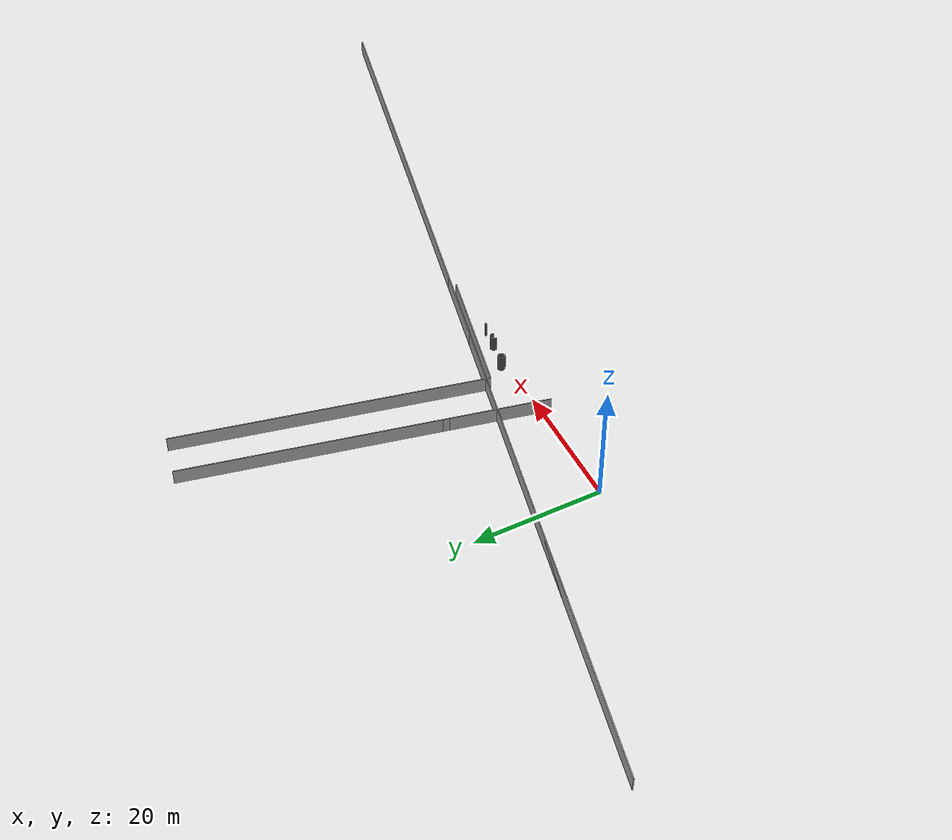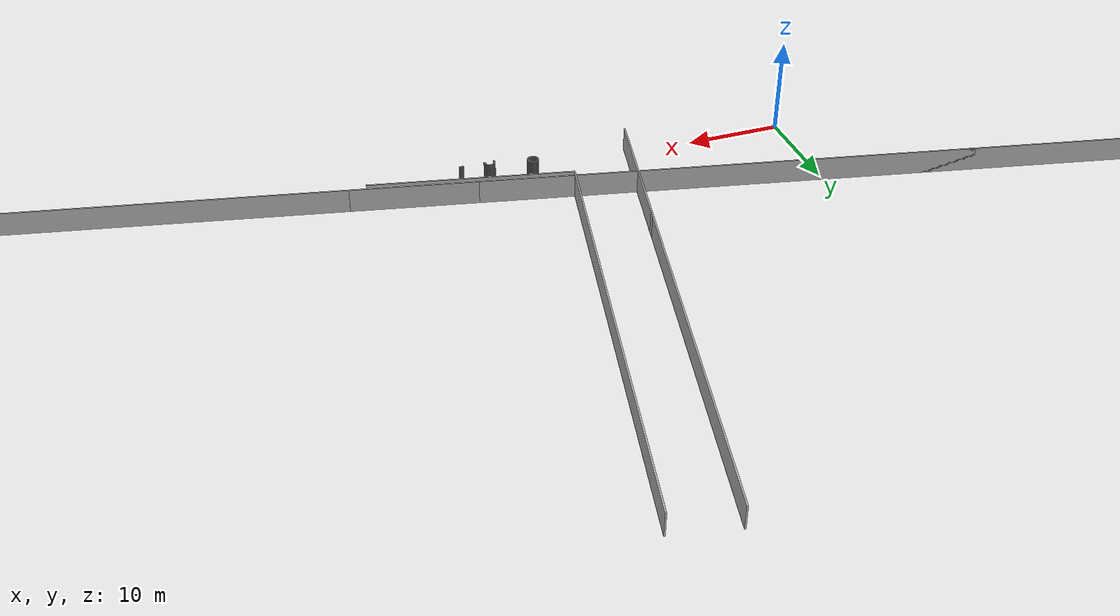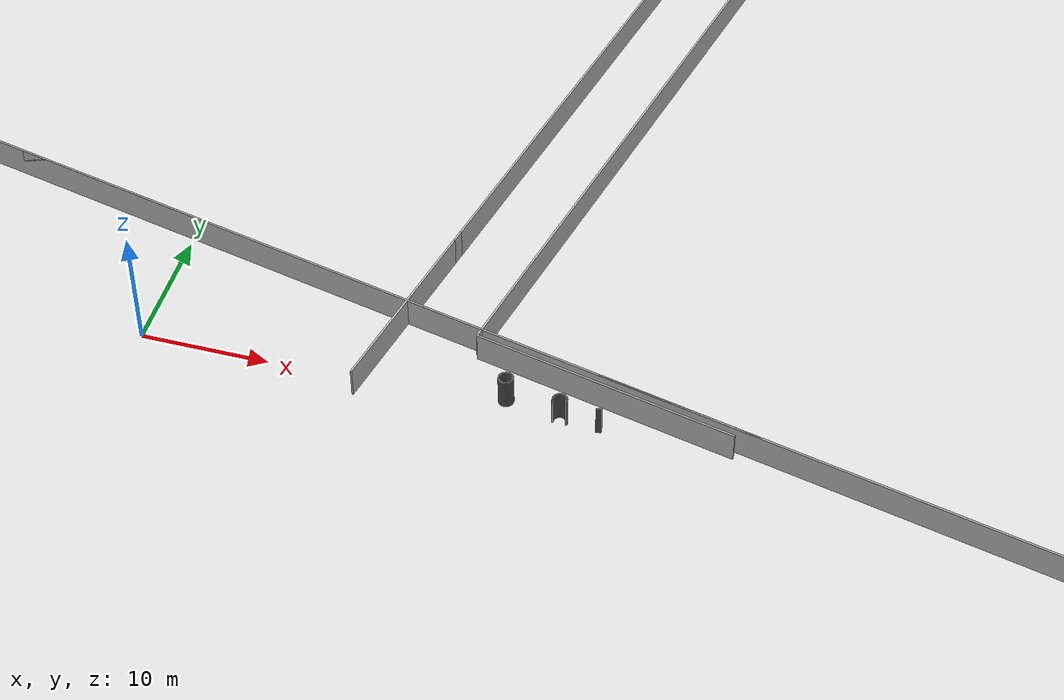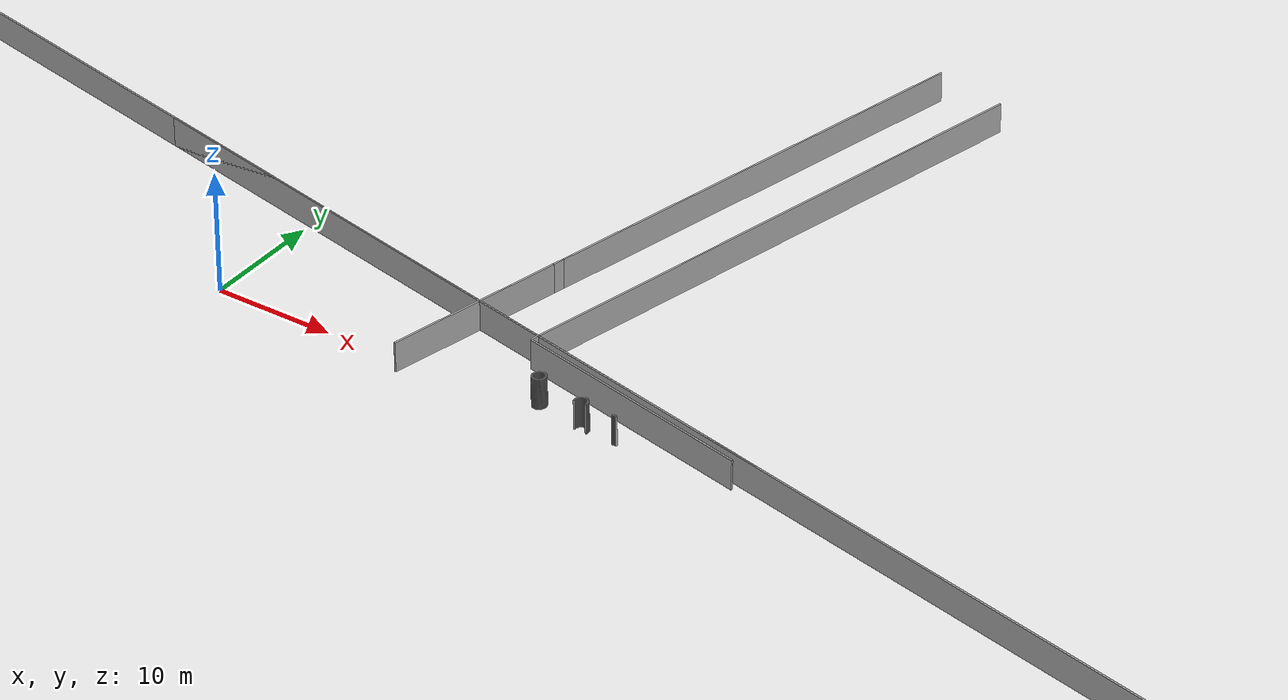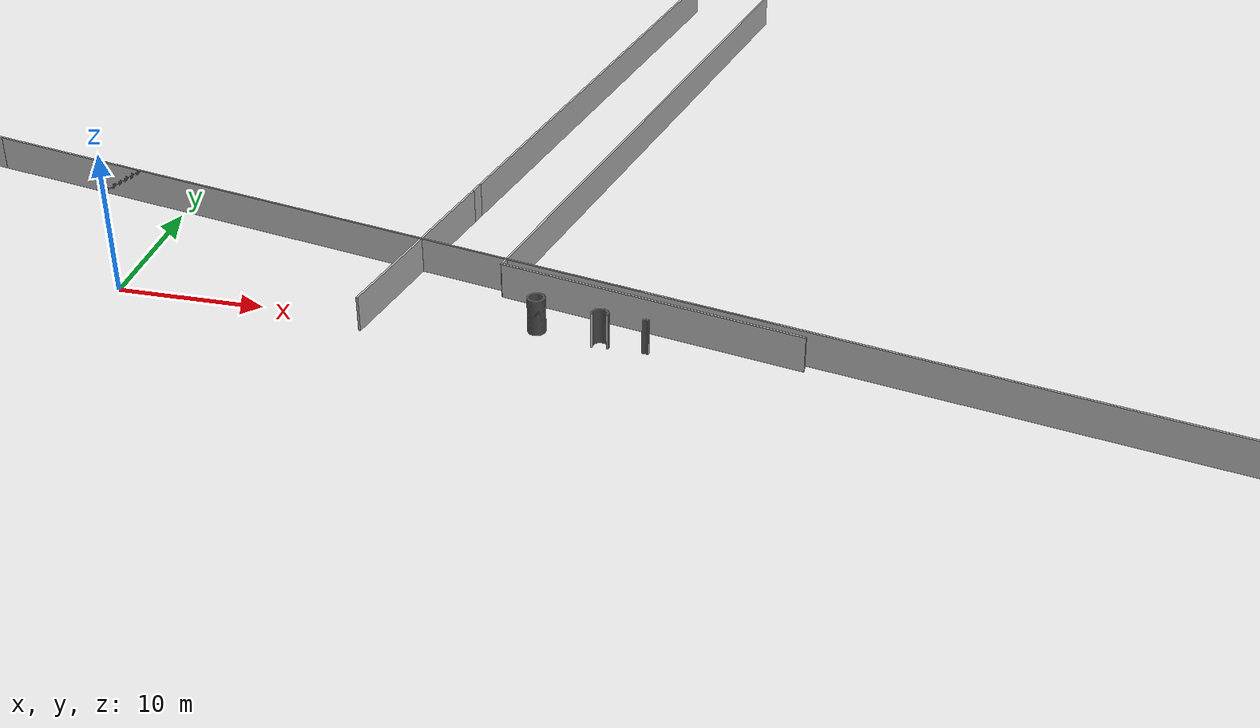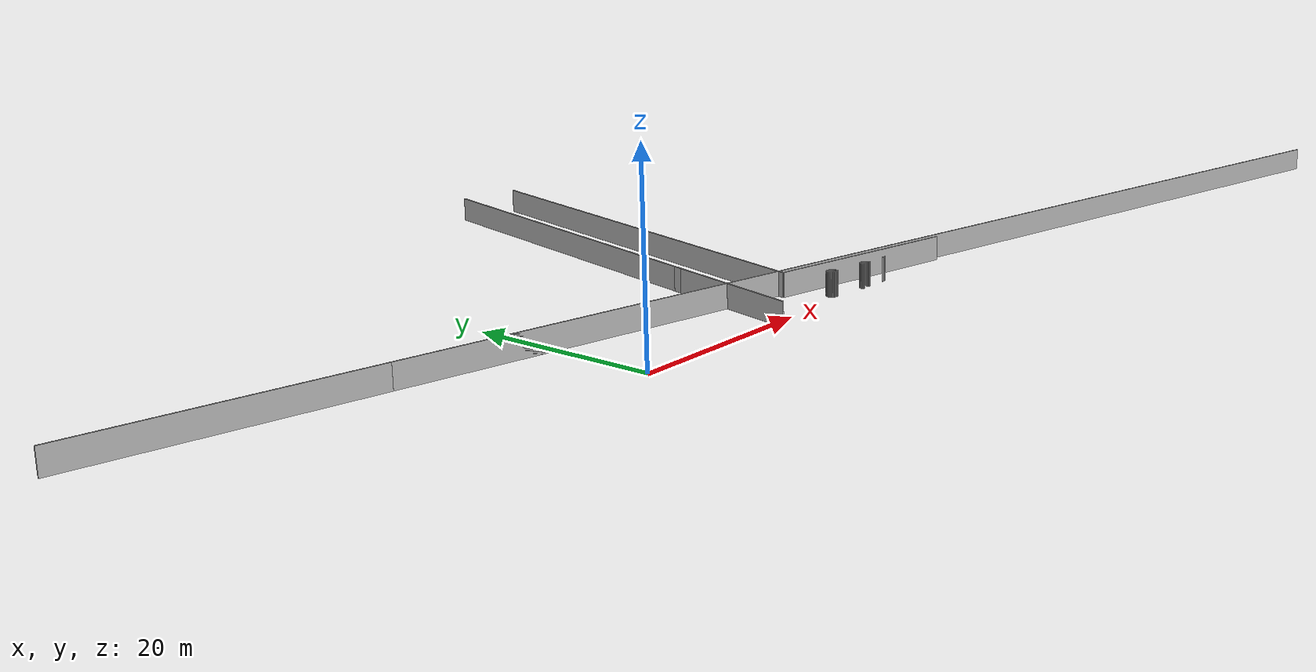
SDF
<?xml version="1.0" ?>
<sdf version="1.6">
  <model name="sps_2604">
    <pose frame="">0 0 0 0 -0 0</pose>
    <static>1</static>
    <self_collide>0</self_collide>
    <allow_auto_disable>0</allow_auto_disable>
    <link name="Wall632">
      <kinematic>0</kinematic>
      <gravity>1</gravity>
      <self_collide>0</self_collide>
      <collision name="collision">
        <geometry>
          <box>
            <size>51.1699 0.15 2.5</size>
          </box>
        </geometry>
        <pose frame="">0 0 0 0 -0 0</pose>
      </collision>
      <visual name="visual">
        <geometry>
          <box>
            <size>51.1699 0.15 2.5</size>
          </box>
        </geometry>
        <pose frame="">0 0 0 0 -0 0</pose>
        <cast_shadows>1</cast_shadows>
        <transparency>0.0</transparency>
      </visual>
      <pose frame="">9.46944 8.65971 1.25 0 0 -0.21425</pose>
    </link>
    <link name="Wall633">
      <kinematic>0</kinematic>
      <gravity>1</gravity>
      <self_collide>0</self_collide>
      <collision name="collision">
        <geometry>
          <box>
            <size>12.9186 0.15 2.5</size>
          </box>
        </geometry>
        <pose frame="">0 0 0 0 -0 0</pose>
      </collision>
      <visual name="visual">
        <geometry>
          <box>
            <size>12.9186 0.15 2.5</size>
          </box>
        </geometry>
        <pose frame="">0 0 0 0 -0 0</pose>
        <cast_shadows>1</cast_shadows>
        <transparency>0.0</transparency>
      </visual>
      <pose frame="">40.7811 1.84662 1.25 0 0 -0.21425</pose>
    </link>
    <link name="Wall978">
      <kinematic>0</kinematic>
      <gravity>1</gravity>
      <self_collide>0</self_collide>
      <collision name="collision">
        <geometry>
          <box>
            <size>48.153 0.15 2.5</size>
          </box>
        </geometry>
        <pose frame="">0 0 0 0 -0 0</pose>
      </collision>
      <visual name="visual">
        <geometry>
          <box>
            <size>48.153 0.15 2.5</size>
          </box>
        </geometry>
        <pose frame="">0 0 0 0 -0 0</pose>
        <cast_shadows>1</cast_shadows>
        <transparency>0.0</transparency>
      </visual>
      <pose frame="">29.9615 28.1377 1.25 0 0 -1.78505</pose>
    </link>
    <link name="Wall979">
      <kinematic>0</kinematic>
      <gravity>1</gravity>
      <self_collide>0</self_collide>
      <collision name="collision">
        <geometry>
          <box>
            <size>20.9004 0.15 2.5</size>
          </box>
        </geometry>
        <pose frame="">0 0 0 0 -0 0</pose>
      </collision>
      <visual name="visual">
        <geometry>
          <box>
            <size>20.9004 0.15 2.5</size>
          </box>
        </geometry>
        <pose frame="">0 0 0 0 -0 0</pose>
        <cast_shadows>1</cast_shadows>
        <transparency>0.0</transparency>
      </visual>
      <pose frame="">35.0537 2.38991 1.25 0 0 -0.214243</pose>
    </link>
    <link name="Wall984">
      <kinematic>0</kinematic>
      <gravity>1</gravity>
      <self_collide>0</self_collide>
      <collision name="collision">
        <geometry>
          <box>
            <size>15.3223 0.15 2.5</size>
          </box>
        </geometry>
        <pose frame="">0 0 0 0 -0 0</pose>
      </collision>
      <visual name="visual">
        <geometry>
          <box>
            <size>15.3223 0.15 2.5</size>
          </box>
        </geometry>
        <pose frame="">0 0 0 0 -0 0</pose>
        <cast_shadows>1</cast_shadows>
        <transparency>0.0</transparency>
      </visual>
      <pose frame="">18.6727 6.17049 1.25 0 -0 1.35655</pose>
    </link>
    <link name="Wall985">
      <kinematic>0</kinematic>
      <gravity>1</gravity>
      <self_collide>0</self_collide>
      <collision name="collision">
        <geometry>
          <box>
            <size>0.97999 0.15 2.5</size>
          </box>
        </geometry>
        <pose frame="">0 0 0 0 -0 0</pose>
      </collision>
      <visual name="visual">
        <geometry>
          <box>
            <size>0.97999 0.15 2.5</size>
          </box>
        </geometry>
        <pose frame="">0 0 0 0 -0 0</pose>
        <cast_shadows>1</cast_shadows>
        <transparency>0.0</transparency>
      </visual>
      <pose frame="">20.4057 14.1353 1.25 0 -0 1.35653</pose>
    </link>
    <link name="Wall986">
      <kinematic>0</kinematic>
      <gravity>1</gravity>
      <self_collide>0</self_collide>
      <collision name="collision">
        <geometry>
          <box>
            <size>39.3005 0.15 2.5</size>
          </box>
        </geometry>
        <pose frame="">0 0 0 0 -0 0</pose>
      </collision>
      <visual name="visual">
        <geometry>
          <box>
            <size>39.3005 0.15 2.5</size>
          </box>
        </geometry>
        <pose frame="">0 0 0 0 -0 0</pose>
        <cast_shadows>1</cast_shadows>
        <transparency>0.0</transparency>
      </visual>
      <pose frame="">24.6878 33.8151 1.25 0 -0 1.35655</pose>
    </link>
    <link name="Wall1416">
      <kinematic>0</kinematic>
      <gravity>1</gravity>
      <self_collide>0</self_collide>
      <collision name="collision">
        <geometry>
          <box>
            <size>0.0454008 0.15 2.5</size>
          </box>
        </geometry>
        <pose frame="">0 0 0 0 -0 0</pose>
      </collision>
      <visual name="visual">
        <geometry>
          <box>
            <size>0.0454008 0.15 2.5</size>
          </box>
        </geometry>
        <pose frame="">0 0 0 0 -0 0</pose>
        <cast_shadows>1</cast_shadows>
        <transparency>0.0</transparency>
      </visual>
      <pose frame="">28.3753 1.5291 1.25 0 0 -0.654794</pose>
    </link>
    <link name="Wall1417">
      <kinematic>0</kinematic>
      <gravity>1</gravity>
      <self_collide>0</self_collide>
      <collision name="collision">
        <geometry>
          <box>
            <size>0.0452735 0.15 2.5</size>
          </box>
        </geometry>
        <pose frame="">0 0 0 0 -0 0</pose>
      </collision>
      <visual name="visual">
        <geometry>
          <box>
            <size>0.0452735 0.15 2.5</size>
          </box>
        </geometry>
        <pose frame="">0 0 0 0 -0 0</pose>
        <cast_shadows>1</cast_shadows>
        <transparency>0.0</transparency>
      </visual>
      <pose frame="">28.41 1.49998 1.25 0 0 -0.741533</pose>
    </link>
    <link name="Wall1418">
      <kinematic>0</kinematic>
      <gravity>1</gravity>
      <self_collide>0</self_collide>
      <collision name="collision">
        <geometry>
          <box>
            <size>0.0452735 0.15 2.5</size>
          </box>
        </geometry>
        <pose frame="">0 0 0 0 -0 0</pose>
      </collision>
      <visual name="visual">
        <geometry>
          <box>
            <size>0.0452735 0.15 2.5</size>
          </box>
        </geometry>
        <pose frame="">0 0 0 0 -0 0</pose>
        <cast_shadows>1</cast_shadows>
        <transparency>0.0</transparency>
      </visual>
      <pose frame="">28.4419 1.468 1.25 0 0 -0.829263</pose>
    </link>
    <link name="Wall1419">
      <kinematic>0</kinematic>
      <gravity>1</gravity>
      <self_collide>0</self_collide>
      <collision name="collision">
        <geometry>
          <box>
            <size>0.0454008 0.15 2.5</size>
          </box>
        </geometry>
        <pose frame="">0 0 0 0 -0 0</pose>
      </collision>
      <visual name="visual">
        <geometry>
          <box>
            <size>0.0454008 0.15 2.5</size>
          </box>
        </geometry>
        <pose frame="">0 0 0 0 -0 0</pose>
        <cast_shadows>1</cast_shadows>
        <transparency>0.0</transparency>
      </visual>
      <pose frame="">28.4711 1.4333 1.25 0 0 -0.916002</pose>
    </link>
    <link name="Wall1420">
      <kinematic>0</kinematic>
      <gravity>1</gravity>
      <self_collide>0</self_collide>
      <collision name="collision">
        <geometry>
          <box>
            <size>0.0454637 0.15 2.5</size>
          </box>
        </geometry>
        <pose frame="">0 0 0 0 -0 0</pose>
      </collision>
      <visual name="visual">
        <geometry>
          <box>
            <size>0.0454637 0.15 2.5</size>
          </box>
        </geometry>
        <pose frame="">0 0 0 0 -0 0</pose>
        <cast_shadows>1</cast_shadows>
        <transparency>0.0</transparency>
      </visual>
      <pose frame="">28.4971 1.3961 1.25 0 0 -1.00551</pose>
    </link>
    <link name="Wall1421">
      <kinematic>0</kinematic>
      <gravity>1</gravity>
      <self_collide>0</self_collide>
      <collision name="collision">
        <geometry>
          <box>
            <size>0.0453724 0.15 2.5</size>
          </box>
        </geometry>
        <pose frame="">0 0 0 0 -0 0</pose>
      </collision>
      <visual name="visual">
        <geometry>
          <box>
            <size>0.0453724 0.15 2.5</size>
          </box>
        </geometry>
        <pose frame="">0 0 0 0 -0 0</pose>
        <cast_shadows>1</cast_shadows>
        <transparency>0.0</transparency>
      </visual>
      <pose frame="">28.5197 1.3568 1.25 0 0 -1.0897</pose>
    </link>
    <link name="Wall1422">
      <kinematic>0</kinematic>
      <gravity>1</gravity>
      <self_collide>0</self_collide>
      <collision name="collision">
        <geometry>
          <box>
            <size>0.0452834 0.15 2.5</size>
          </box>
        </geometry>
        <pose frame="">0 0 0 0 -0 0</pose>
      </collision>
      <visual name="visual">
        <geometry>
          <box>
            <size>0.0452834 0.15 2.5</size>
          </box>
        </geometry>
        <pose frame="">0 0 0 0 -0 0</pose>
        <cast_shadows>1</cast_shadows>
        <transparency>0.0</transparency>
      </visual>
      <pose frame="">28.5389 1.31578 1.25 0 0 -1.17652</pose>
    </link>
    <link name="Wall1423">
      <kinematic>0</kinematic>
      <gravity>1</gravity>
      <self_collide>0</self_collide>
      <collision name="collision">
        <geometry>
          <box>
            <size>0.0454804 0.15 2.5</size>
          </box>
        </geometry>
        <pose frame="">0 0 0 0 -0 0</pose>
      </collision>
      <visual name="visual">
        <geometry>
          <box>
            <size>0.0454804 0.15 2.5</size>
          </box>
        </geometry>
        <pose frame="">0 0 0 0 -0 0</pose>
        <cast_shadows>1</cast_shadows>
        <transparency>0.0</transparency>
      </visual>
      <pose frame="">28.5544 1.27318 1.25 0 0 -1.26687</pose>
    </link>
    <link name="Wall1424">
      <kinematic>0</kinematic>
      <gravity>1</gravity>
      <self_collide>0</self_collide>
      <collision name="collision">
        <geometry>
          <box>
            <size>0.0452689 0.15 2.5</size>
          </box>
        </geometry>
        <pose frame="">0 0 0 0 -0 0</pose>
      </collision>
      <visual name="visual">
        <geometry>
          <box>
            <size>0.0452689 0.15 2.5</size>
          </box>
        </geometry>
        <pose frame="">0 0 0 0 -0 0</pose>
        <cast_shadows>1</cast_shadows>
        <transparency>0.0</transparency>
      </visual>
      <pose frame="">28.5662 1.22938 1.25 0 0 -1.35198</pose>
    </link>
    <link name="Wall1425">
      <kinematic>0</kinematic>
      <gravity>1</gravity>
      <self_collide>0</self_collide>
      <collision name="collision">
        <geometry>
          <box>
            <size>0.0453551 0.15 2.5</size>
          </box>
        </geometry>
        <pose frame="">0 0 0 0 -0 0</pose>
      </collision>
      <visual name="visual">
        <geometry>
          <box>
            <size>0.0453551 0.15 2.5</size>
          </box>
        </geometry>
        <pose frame="">0 0 0 0 -0 0</pose>
        <cast_shadows>1</cast_shadows>
        <transparency>0.0</transparency>
      </visual>
      <pose frame="">28.574 1.1848 1.25 0 0 -1.4426</pose>
    </link>
    <link name="Wall1426">
      <kinematic>0</kinematic>
      <gravity>1</gravity>
      <self_collide>0</self_collide>
      <collision name="collision">
        <geometry>
          <box>
            <size>0.0454548 0.15 2.5</size>
          </box>
        </geometry>
        <pose frame="">0 0 0 0 -0 0</pose>
      </collision>
      <visual name="visual">
        <geometry>
          <box>
            <size>0.0454548 0.15 2.5</size>
          </box>
        </geometry>
        <pose frame="">0 0 0 0 -0 0</pose>
        <cast_shadows>1</cast_shadows>
        <transparency>0.0</transparency>
      </visual>
      <pose frame="">28.5779 1.1396 1.25 0 0 -1.52647</pose>
    </link>
    <link name="Wall1427">
      <kinematic>0</kinematic>
      <gravity>1</gravity>
      <self_collide>0</self_collide>
      <collision name="collision">
        <geometry>
          <box>
            <size>0.0452719 0.15 2.5</size>
          </box>
        </geometry>
        <pose frame="">0 0 0 0 -0 0</pose>
      </collision>
      <visual name="visual">
        <geometry>
          <box>
            <size>0.0452719 0.15 2.5</size>
          </box>
        </geometry>
        <pose frame="">0 0 0 0 -0 0</pose>
        <cast_shadows>1</cast_shadows>
        <transparency>0.0</transparency>
      </visual>
      <pose frame="">28.5779 1.09428 1.25 0 0 -1.6153</pose>
    </link>
    <link name="Wall1428">
      <kinematic>0</kinematic>
      <gravity>1</gravity>
      <self_collide>0</self_collide>
      <collision name="collision">
        <geometry>
          <box>
            <size>0.0453788 0.15 2.5</size>
          </box>
        </geometry>
        <pose frame="">0 0 0 0 -0 0</pose>
      </collision>
      <visual name="visual">
        <geometry>
          <box>
            <size>0.0453788 0.15 2.5</size>
          </box>
        </geometry>
        <pose frame="">0 0 0 0 -0 0</pose>
        <cast_shadows>1</cast_shadows>
        <transparency>0.0</transparency>
      </visual>
      <pose frame="">28.5739 1.04918 1.25 0 0 -1.70299</pose>
    </link>
    <link name="Wall1429">
      <kinematic>0</kinematic>
      <gravity>1</gravity>
      <self_collide>0</self_collide>
      <collision name="collision">
        <geometry>
          <box>
            <size>0.0454476 0.15 2.5</size>
          </box>
        </geometry>
        <pose frame="">0 0 0 0 -0 0</pose>
      </collision>
      <visual name="visual">
        <geometry>
          <box>
            <size>0.0454476 0.15 2.5</size>
          </box>
        </geometry>
        <pose frame="">0 0 0 0 -0 0</pose>
        <cast_shadows>1</cast_shadows>
        <transparency>0.0</transparency>
      </visual>
      <pose frame="">28.566 1.0045 1.25 0 0 -1.78874</pose>
    </link>
    <link name="Wall1430">
      <kinematic>0</kinematic>
      <gravity>1</gravity>
      <self_collide>0</self_collide>
      <collision name="collision">
        <geometry>
          <box>
            <size>0.0453057 0.15 2.5</size>
          </box>
        </geometry>
        <pose frame="">0 0 0 0 -0 0</pose>
      </collision>
      <visual name="visual">
        <geometry>
          <box>
            <size>0.0453057 0.15 2.5</size>
          </box>
        </geometry>
        <pose frame="">0 0 0 0 -0 0</pose>
        <cast_shadows>1</cast_shadows>
        <transparency>0.0</transparency>
      </visual>
      <pose frame="">28.5543 0.960708 1.25 0 0 -1.87593</pose>
    </link>
    <link name="Wall1431">
      <kinematic>0</kinematic>
      <gravity>1</gravity>
      <self_collide>0</self_collide>
      <collision name="collision">
        <geometry>
          <box>
            <size>0.0452834 0.15 2.5</size>
          </box>
        </geometry>
        <pose frame="">0 0 0 0 -0 0</pose>
      </collision>
      <visual name="visual">
        <geometry>
          <box>
            <size>0.0452834 0.15 2.5</size>
          </box>
        </geometry>
        <pose frame="">0 0 0 0 -0 0</pose>
        <cast_shadows>1</cast_shadows>
        <transparency>0.0</transparency>
      </visual>
      <pose frame="">28.5387 0.918197 1.25 0 0 -1.96507</pose>
    </link>
    <link name="Wall1432">
      <kinematic>0</kinematic>
      <gravity>1</gravity>
      <self_collide>0</self_collide>
      <collision name="collision">
        <geometry>
          <box>
            <size>0.045288 0.15 2.5</size>
          </box>
        </geometry>
        <pose frame="">0 0 0 0 -0 0</pose>
      </collision>
      <visual name="visual">
        <geometry>
          <box>
            <size>0.045288 0.15 2.5</size>
          </box>
        </geometry>
        <pose frame="">0 0 0 0 -0 0</pose>
        <cast_shadows>1</cast_shadows>
        <transparency>0.0</transparency>
      </visual>
      <pose frame="">28.5196 0.877181 1.25 0 0 -2.04831</pose>
    </link>
    <link name="Wall1433">
      <kinematic>0</kinematic>
      <gravity>1</gravity>
      <self_collide>0</self_collide>
      <collision name="collision">
        <geometry>
          <box>
            <size>0.0455949 0.15 2.5</size>
          </box>
        </geometry>
        <pose frame="">0 0 0 0 -0 0</pose>
      </collision>
      <visual name="visual">
        <geometry>
          <box>
            <size>0.0455949 0.15 2.5</size>
          </box>
        </geometry>
        <pose frame="">0 0 0 0 -0 0</pose>
        <cast_shadows>1</cast_shadows>
        <transparency>0.0</transparency>
      </visual>
      <pose frame="">28.4969 0.837874 1.25 0 0 -2.14061</pose>
    </link>
    <link name="Wall1434">
      <kinematic>0</kinematic>
      <gravity>1</gravity>
      <self_collide>0</self_collide>
      <collision name="collision">
        <geometry>
          <box>
            <size>0.0453637 0.15 2.5</size>
          </box>
        </geometry>
        <pose frame="">0 0 0 0 -0 0</pose>
      </collision>
      <visual name="visual">
        <geometry>
          <box>
            <size>0.0453637 0.15 2.5</size>
          </box>
        </geometry>
        <pose frame="">0 0 0 0 -0 0</pose>
        <cast_shadows>1</cast_shadows>
        <transparency>0.0</transparency>
      </visual>
      <pose frame="">28.4708 0.800673 1.25 0 0 -2.22452</pose>
    </link>
    <link name="Wall1435">
      <kinematic>0</kinematic>
      <gravity>1</gravity>
      <self_collide>0</self_collide>
      <collision name="collision">
        <geometry>
          <box>
            <size>0.0452735 0.15 2.5</size>
          </box>
        </geometry>
        <pose frame="">0 0 0 0 -0 0</pose>
      </collision>
      <visual name="visual">
        <geometry>
          <box>
            <size>0.0452735 0.15 2.5</size>
          </box>
        </geometry>
        <pose frame="">0 0 0 0 -0 0</pose>
        <cast_shadows>1</cast_shadows>
        <transparency>0.0</transparency>
      </visual>
      <pose frame="">28.4418 0.765975 1.25 0 0 -2.31233</pose>
    </link>
    <link name="Wall1436">
      <kinematic>0</kinematic>
      <gravity>1</gravity>
      <self_collide>0</self_collide>
      <collision name="collision">
        <geometry>
          <box>
            <size>0.0453186 0.15 2.5</size>
          </box>
        </geometry>
        <pose frame="">0 0 0 0 -0 0</pose>
      </collision>
      <visual name="visual">
        <geometry>
          <box>
            <size>0.0453186 0.15 2.5</size>
          </box>
        </geometry>
        <pose frame="">0 0 0 0 -0 0</pose>
        <cast_shadows>1</cast_shadows>
        <transparency>0.0</transparency>
      </visual>
      <pose frame="">28.4098 0.733992 1.25 0 0 -2.40097</pose>
    </link>
    <link name="Wall1437">
      <kinematic>0</kinematic>
      <gravity>1</gravity>
      <self_collide>0</self_collide>
      <collision name="collision">
        <geometry>
          <box>
            <size>0.0453153 0.15 2.5</size>
          </box>
        </geometry>
        <pose frame="">0 0 0 0 -0 0</pose>
      </collision>
      <visual name="visual">
        <geometry>
          <box>
            <size>0.0453153 0.15 2.5</size>
          </box>
        </geometry>
        <pose frame="">0 0 0 0 -0 0</pose>
        <cast_shadows>1</cast_shadows>
        <transparency>0.0</transparency>
      </visual>
      <pose frame="">28.3751 0.704909 1.25 0 0 -2.48705</pose>
    </link>
    <link name="Wall1438">
      <kinematic>0</kinematic>
      <gravity>1</gravity>
      <self_collide>0</self_collide>
      <collision name="collision">
        <geometry>
          <box>
            <size>0.0455479 0.15 2.5</size>
          </box>
        </geometry>
        <pose frame="">0 0 0 0 -0 0</pose>
      </collision>
      <visual name="visual">
        <geometry>
          <box>
            <size>0.0455479 0.15 2.5</size>
          </box>
        </geometry>
        <pose frame="">0 0 0 0 -0 0</pose>
        <cast_shadows>1</cast_shadows>
        <transparency>0.0</transparency>
      </visual>
      <pose frame="">28.3379 0.678908 1.25 0 0 -2.57589</pose>
    </link>
    <link name="Wall1439">
      <kinematic>0</kinematic>
      <gravity>1</gravity>
      <self_collide>0</self_collide>
      <collision name="collision">
        <geometry>
          <box>
            <size>0.0453183 0.15 2.5</size>
          </box>
        </geometry>
        <pose frame="">0 0 0 0 -0 0</pose>
      </collision>
      <visual name="visual">
        <geometry>
          <box>
            <size>0.0453183 0.15 2.5</size>
          </box>
        </geometry>
        <pose frame="">0 0 0 0 -0 0</pose>
        <cast_shadows>1</cast_shadows>
        <transparency>0.0</transparency>
      </visual>
      <pose frame="">28.2985 0.656203 1.25 0 0 -2.65987</pose>
    </link>
    <link name="Wall1440">
      <kinematic>0</kinematic>
      <gravity>1</gravity>
      <self_collide>0</self_collide>
      <collision name="collision">
        <geometry>
          <box>
            <size>0.0452134 0.15 2.5</size>
          </box>
        </geometry>
        <pose frame="">0 0 0 0 -0 0</pose>
      </collision>
      <visual name="visual">
        <geometry>
          <box>
            <size>0.0452134 0.15 2.5</size>
          </box>
        </geometry>
        <pose frame="">0 0 0 0 -0 0</pose>
        <cast_shadows>1</cast_shadows>
        <transparency>0.0</transparency>
      </visual>
      <pose frame="">28.2576 0.637099 1.25 0 0 -2.75106</pose>
    </link>
    <link name="Wall1441">
      <kinematic>0</kinematic>
      <gravity>1</gravity>
      <self_collide>0</self_collide>
      <collision name="collision">
        <geometry>
          <box>
            <size>0.0455355 0.15 2.5</size>
          </box>
        </geometry>
        <pose frame="">0 0 0 0 -0 0</pose>
      </collision>
      <visual name="visual">
        <geometry>
          <box>
            <size>0.0455355 0.15 2.5</size>
          </box>
        </geometry>
        <pose frame="">0 0 0 0 -0 0</pose>
        <cast_shadows>1</cast_shadows>
        <transparency>0.0</transparency>
      </visual>
      <pose frame="">28.215 0.621596 1.25 0 0 -2.83383</pose>
    </link>
    <link name="Wall1442">
      <kinematic>0</kinematic>
      <gravity>1</gravity>
      <self_collide>0</self_collide>
      <collision name="collision">
        <geometry>
          <box>
            <size>0.0452689 0.15 2.5</size>
          </box>
        </geometry>
        <pose frame="">0 0 0 0 -0 0</pose>
      </collision>
      <visual name="visual">
        <geometry>
          <box>
            <size>0.0452689 0.15 2.5</size>
          </box>
        </geometry>
        <pose frame="">0 0 0 0 -0 0</pose>
        <cast_shadows>1</cast_shadows>
        <transparency>0.0</transparency>
      </visual>
      <pose frame="">28.1712 0.609786 1.25 0 0 -2.92278</pose>
    </link>
    <link name="Wall1443">
      <kinematic>0</kinematic>
      <gravity>1</gravity>
      <self_collide>0</self_collide>
      <collision name="collision">
        <geometry>
          <box>
            <size>0.0454156 0.15 2.5</size>
          </box>
        </geometry>
        <pose frame="">0 0 0 0 -0 0</pose>
      </collision>
      <visual name="visual">
        <geometry>
          <box>
            <size>0.0454156 0.15 2.5</size>
          </box>
        </geometry>
        <pose frame="">0 0 0 0 -0 0</pose>
        <cast_shadows>1</cast_shadows>
        <transparency>0.0</transparency>
      </visual>
      <pose frame="">28.1265 0.601973 1.25 0 0 -3.01357</pose>
    </link>
    <link name="Wall1444">
      <kinematic>0</kinematic>
      <gravity>1</gravity>
      <self_collide>0</self_collide>
      <collision name="collision">
        <geometry>
          <box>
            <size>0.0453912 0.15 2.5</size>
          </box>
        </geometry>
        <pose frame="">0 0 0 0 -0 0</pose>
      </collision>
      <visual name="visual">
        <geometry>
          <box>
            <size>0.0453912 0.15 2.5</size>
          </box>
        </geometry>
        <pose frame="">0 0 0 0 -0 0</pose>
        <cast_shadows>1</cast_shadows>
        <transparency>0.0</transparency>
      </visual>
      <pose frame="">28.0814 0.598098 1.25 0 0 -3.09855</pose>
    </link>
    <link name="Wall1445">
      <kinematic>0</kinematic>
      <gravity>1</gravity>
      <self_collide>0</self_collide>
      <collision name="collision">
        <geometry>
          <box>
            <size>0.0452692 0.15 2.5</size>
          </box>
        </geometry>
        <pose frame="">0 0 0 0 -0 0</pose>
      </collision>
      <visual name="visual">
        <geometry>
          <box>
            <size>0.0452692 0.15 2.5</size>
          </box>
        </geometry>
        <pose frame="">0 0 0 0 -0 0</pose>
        <cast_shadows>1</cast_shadows>
        <transparency>0.0</transparency>
      </visual>
      <pose frame="">28.0361 0.598098 1.25 0 -0 3.09843</pose>
    </link>
    <link name="Wall1446">
      <kinematic>0</kinematic>
      <gravity>1</gravity>
      <self_collide>0</self_collide>
      <collision name="collision">
        <geometry>
          <box>
            <size>0.0453869 0.15 2.5</size>
          </box>
        </geometry>
        <pose frame="">0 0 0 0 -0 0</pose>
      </collision>
      <visual name="visual">
        <geometry>
          <box>
            <size>0.0453869 0.15 2.5</size>
          </box>
        </geometry>
        <pose frame="">0 0 0 0 -0 0</pose>
        <cast_shadows>1</cast_shadows>
        <transparency>0.0</transparency>
      </visual>
      <pose frame="">27.991 0.602096 1.25 0 -0 3.00806</pose>
    </link>
    <link name="Wall1447">
      <kinematic>0</kinematic>
      <gravity>1</gravity>
      <self_collide>0</self_collide>
      <collision name="collision">
        <geometry>
          <box>
            <size>0.0454941 0.15 2.5</size>
          </box>
        </geometry>
        <pose frame="">0 0 0 0 -0 0</pose>
      </collision>
      <visual name="visual">
        <geometry>
          <box>
            <size>0.0454941 0.15 2.5</size>
          </box>
        </geometry>
        <pose frame="">0 0 0 0 -0 0</pose>
        <cast_shadows>1</cast_shadows>
        <transparency>0.0</transparency>
      </visual>
      <pose frame="">27.9463 0.61 1.25 0 -0 2.92525</pose>
    </link>
    <link name="Wall1448">
      <kinematic>0</kinematic>
      <gravity>1</gravity>
      <self_collide>0</self_collide>
      <collision name="collision">
        <geometry>
          <box>
            <size>0.0452475 0.15 2.5</size>
          </box>
        </geometry>
        <pose frame="">0 0 0 0 -0 0</pose>
      </collision>
      <visual name="visual">
        <geometry>
          <box>
            <size>0.0452475 0.15 2.5</size>
          </box>
        </geometry>
        <pose frame="">0 0 0 0 -0 0</pose>
        <cast_shadows>1</cast_shadows>
        <transparency>0.0</transparency>
      </visual>
      <pose frame="">27.9025 0.621688 1.25 0 -0 2.83605</pose>
    </link>
    <link name="Wall1449">
      <kinematic>0</kinematic>
      <gravity>1</gravity>
      <self_collide>0</self_collide>
      <collision name="collision">
        <geometry>
          <box>
            <size>0.0452834 0.15 2.5</size>
          </box>
        </geometry>
        <pose frame="">0 0 0 0 -0 0</pose>
      </collision>
      <visual name="visual">
        <geometry>
          <box>
            <size>0.0452834 0.15 2.5</size>
          </box>
        </geometry>
        <pose frame="">0 0 0 0 -0 0</pose>
        <cast_shadows>1</cast_shadows>
        <transparency>0.0</transparency>
      </visual>
      <pose frame="">27.86 0.637191 1.25 0 -0 2.74732</pose>
    </link>
    <link name="Wall1450">
      <kinematic>0</kinematic>
      <gravity>1</gravity>
      <self_collide>0</self_collide>
      <collision name="collision">
        <geometry>
          <box>
            <size>0.0455348 0.15 2.5</size>
          </box>
        </geometry>
        <pose frame="">0 0 0 0 -0 0</pose>
      </collision>
      <visual name="visual">
        <geometry>
          <box>
            <size>0.0455348 0.15 2.5</size>
          </box>
        </geometry>
        <pose frame="">0 0 0 0 -0 0</pose>
        <cast_shadows>1</cast_shadows>
        <transparency>0.0</transparency>
      </visual>
      <pose frame="">27.8189 0.656386 1.25 0 -0 2.66236</pose>
    </link>
    <link name="Wall1451">
      <kinematic>0</kinematic>
      <gravity>1</gravity>
      <self_collide>0</self_collide>
      <collision name="collision">
        <geometry>
          <box>
            <size>0.045342 0.15 2.5</size>
          </box>
        </geometry>
        <pose frame="">0 0 0 0 -0 0</pose>
      </collision>
      <visual name="visual">
        <geometry>
          <box>
            <size>0.045342 0.15 2.5</size>
          </box>
        </geometry>
        <pose frame="">0 0 0 0 -0 0</pose>
        <cast_shadows>1</cast_shadows>
        <transparency>0.0</transparency>
      </visual>
      <pose frame="">27.7796 0.679091 1.25 0 -0 2.57301</pose>
    </link>
    <link name="Wall1452">
      <kinematic>0</kinematic>
      <gravity>1</gravity>
      <self_collide>0</self_collide>
      <collision name="collision">
        <geometry>
          <box>
            <size>0.0453637 0.15 2.5</size>
          </box>
        </geometry>
        <pose frame="">0 0 0 0 -0 0</pose>
      </collision>
      <visual name="visual">
        <geometry>
          <box>
            <size>0.0453637 0.15 2.5</size>
          </box>
        </geometry>
        <pose frame="">0 0 0 0 -0 0</pose>
        <cast_shadows>1</cast_shadows>
        <transparency>0.0</transparency>
      </visual>
      <pose frame="">27.7425 0.705092 1.25 0 -0 2.48787</pose>
    </link>
    <link name="Wall1453">
      <kinematic>0</kinematic>
      <gravity>1</gravity>
      <self_collide>0</self_collide>
      <collision name="collision">
        <geometry>
          <box>
            <size>0.0452735 0.15 2.5</size>
          </box>
        </geometry>
        <pose frame="">0 0 0 0 -0 0</pose>
      </collision>
      <visual name="visual">
        <geometry>
          <box>
            <size>0.0452735 0.15 2.5</size>
          </box>
        </geometry>
        <pose frame="">0 0 0 0 -0 0</pose>
        <cast_shadows>1</cast_shadows>
        <transparency>0.0</transparency>
      </visual>
      <pose frame="">27.7078 0.734176 1.25 0 -0 2.40006</pose>
    </link>
    <link name="Wall1454">
      <kinematic>0</kinematic>
      <gravity>1</gravity>
      <self_collide>0</self_collide>
      <collision name="collision">
        <geometry>
          <box>
            <size>0.0453186 0.15 2.5</size>
          </box>
        </geometry>
        <pose frame="">0 0 0 0 -0 0</pose>
      </collision>
      <visual name="visual">
        <geometry>
          <box>
            <size>0.0453186 0.15 2.5</size>
          </box>
        </geometry>
        <pose frame="">0 0 0 0 -0 0</pose>
        <cast_shadows>1</cast_shadows>
        <transparency>0.0</transparency>
      </visual>
      <pose frame="">27.6758 0.766189 1.25 0 -0 2.31142</pose>
    </link>
    <link name="Wall1455">
      <kinematic>0</kinematic>
      <gravity>1</gravity>
      <self_collide>0</self_collide>
      <collision name="collision">
        <geometry>
          <box>
            <size>0.0454008 0.15 2.5</size>
          </box>
        </geometry>
        <pose frame="">0 0 0 0 -0 0</pose>
      </collision>
      <visual name="visual">
        <geometry>
          <box>
            <size>0.0454008 0.15 2.5</size>
          </box>
        </geometry>
        <pose frame="">0 0 0 0 -0 0</pose>
        <cast_shadows>1</cast_shadows>
        <transparency>0.0</transparency>
      </visual>
      <pose frame="">27.6467 0.800918 1.25 0 -0 2.22559</pose>
    </link>
    <link name="Wall1456">
      <kinematic>0</kinematic>
      <gravity>1</gravity>
      <self_collide>0</self_collide>
      <collision name="collision">
        <geometry>
          <box>
            <size>0.0454637 0.15 2.5</size>
          </box>
        </geometry>
        <pose frame="">0 0 0 0 -0 0</pose>
      </collision>
      <visual name="visual">
        <geometry>
          <box>
            <size>0.0454637 0.15 2.5</size>
          </box>
        </geometry>
        <pose frame="">0 0 0 0 -0 0</pose>
        <cast_shadows>1</cast_shadows>
        <transparency>0.0</transparency>
      </visual>
      <pose frame="">27.6207 0.838118 1.25 0 -0 2.13608</pose>
    </link>
    <link name="Wall1457">
      <kinematic>0</kinematic>
      <gravity>1</gravity>
      <self_collide>0</self_collide>
      <collision name="collision">
        <geometry>
          <box>
            <size>0.0453183 0.15 2.5</size>
          </box>
        </geometry>
        <pose frame="">0 0 0 0 -0 0</pose>
      </collision>
      <visual name="visual">
        <geometry>
          <box>
            <size>0.0453183 0.15 2.5</size>
          </box>
        </geometry>
        <pose frame="">0 0 0 0 -0 0</pose>
        <cast_shadows>1</cast_shadows>
        <transparency>0.0</transparency>
      </visual>
      <pose frame="">27.598 0.877395 1.25 0 -0 2.05251</pose>
    </link>
    <link name="Wall1458">
      <kinematic>0</kinematic>
      <gravity>1</gravity>
      <self_collide>0</self_collide>
      <collision name="collision">
        <geometry>
          <box>
            <size>0.0453827 0.15 2.5</size>
          </box>
        </geometry>
        <pose frame="">0 0 0 0 -0 0</pose>
      </collision>
      <visual name="visual">
        <geometry>
          <box>
            <size>0.0453827 0.15 2.5</size>
          </box>
        </geometry>
        <pose frame="">0 0 0 0 -0 0</pose>
        <cast_shadows>1</cast_shadows>
        <transparency>0.0</transparency>
      </visual>
      <pose frame="">27.5789 0.918471 1.25 0 -0 1.95979</pose>
    </link>
    <link name="Wall1459">
      <kinematic>0</kinematic>
      <gravity>1</gravity>
      <self_collide>0</self_collide>
      <collision name="collision">
        <geometry>
          <box>
            <size>0.0453611 0.15 2.5</size>
          </box>
        </geometry>
        <pose frame="">0 0 0 0 -0 0</pose>
      </collision>
      <visual name="visual">
        <geometry>
          <box>
            <size>0.0453611 0.15 2.5</size>
          </box>
        </geometry>
        <pose frame="">0 0 0 0 -0 0</pose>
        <cast_shadows>1</cast_shadows>
        <transparency>0.0</transparency>
      </visual>
      <pose frame="">27.5634 0.961074 1.25 0 -0 1.87978</pose>
    </link>
    <link name="Wall1460">
      <kinematic>0</kinematic>
      <gravity>1</gravity>
      <self_collide>0</self_collide>
      <collision name="collision">
        <geometry>
          <box>
            <size>0.0452295 0.15 2.5</size>
          </box>
        </geometry>
        <pose frame="">0 0 0 0 -0 0</pose>
      </collision>
      <visual name="visual">
        <geometry>
          <box>
            <size>0.0452295 0.15 2.5</size>
          </box>
        </geometry>
        <pose frame="">0 0 0 0 -0 0</pose>
        <cast_shadows>1</cast_shadows>
        <transparency>0.0</transparency>
      </visual>
      <pose frame="">27.5517 1.00477 1.25 0 -0 1.78566</pose>
    </link>
    <link name="Wall1461">
      <kinematic>0</kinematic>
      <gravity>1</gravity>
      <self_collide>0</self_collide>
      <collision name="collision">
        <geometry>
          <box>
            <size>0.0454394 0.15 2.5</size>
          </box>
        </geometry>
        <pose frame="">0 0 0 0 -0 0</pose>
      </collision>
      <visual name="visual">
        <geometry>
          <box>
            <size>0.0454394 0.15 2.5</size>
          </box>
        </geometry>
        <pose frame="">0 0 0 0 -0 0</pose>
        <cast_shadows>1</cast_shadows>
        <transparency>0.0</transparency>
      </visual>
      <pose frame="">27.5438 1.04939 1.25 0 -0 1.70282</pose>
    </link>
    <link name="Wall1462">
      <kinematic>0</kinematic>
      <gravity>1</gravity>
      <self_collide>0</self_collide>
      <collision name="collision">
        <geometry>
          <box>
            <size>0.0453938 0.15 2.5</size>
          </box>
        </geometry>
        <pose frame="">0 0 0 0 -0 0</pose>
      </collision>
      <visual name="visual">
        <geometry>
          <box>
            <size>0.0453938 0.15 2.5</size>
          </box>
        </geometry>
        <pose frame="">0 0 0 0 -0 0</pose>
        <cast_shadows>1</cast_shadows>
        <transparency>0.0</transparency>
      </visual>
      <pose frame="">27.5398 1.09459 1.25 0 -0 1.61518</pose>
    </link>
    <link name="Wall1463">
      <kinematic>0</kinematic>
      <gravity>1</gravity>
      <self_collide>0</self_collide>
      <collision name="collision">
        <geometry>
          <box>
            <size>0.0454548 0.15 2.5</size>
          </box>
        </geometry>
        <pose frame="">0 0 0 0 -0 0</pose>
      </collision>
      <visual name="visual">
        <geometry>
          <box>
            <size>0.0454548 0.15 2.5</size>
          </box>
        </geometry>
        <pose frame="">0 0 0 0 -0 0</pose>
        <cast_shadows>1</cast_shadows>
        <transparency>0.0</transparency>
      </visual>
      <pose frame="">27.5398 1.13997 1.25 0 -0 1.52647</pose>
    </link>
    <link name="Wall1464">
      <kinematic>0</kinematic>
      <gravity>1</gravity>
      <self_collide>0</self_collide>
      <collision name="collision">
        <geometry>
          <box>
            <size>0.0451973 0.15 2.5</size>
          </box>
        </geometry>
        <pose frame="">0 0 0 0 -0 0</pose>
      </collision>
      <visual name="visual">
        <geometry>
          <box>
            <size>0.0451973 0.15 2.5</size>
          </box>
        </geometry>
        <pose frame="">0 0 0 0 -0 0</pose>
        <cast_shadows>1</cast_shadows>
        <transparency>0.0</transparency>
      </visual>
      <pose frame="">27.5438 1.18507 1.25 0 -0 1.43807</pose>
    </link>
    <link name="Wall1465">
      <kinematic>0</kinematic>
      <gravity>1</gravity>
      <self_collide>0</self_collide>
      <collision name="collision">
        <geometry>
          <box>
            <size>0.0455072 0.15 2.5</size>
          </box>
        </geometry>
        <pose frame="">0 0 0 0 -0 0</pose>
      </collision>
      <visual name="visual">
        <geometry>
          <box>
            <size>0.0455072 0.15 2.5</size>
          </box>
        </geometry>
        <pose frame="">0 0 0 0 -0 0</pose>
        <cast_shadows>1</cast_shadows>
        <transparency>0.0</transparency>
      </visual>
      <pose frame="">27.5517 1.22969 1.25 0 -0 1.35315</pose>
    </link>
    <link name="Wall1466">
      <kinematic>0</kinematic>
      <gravity>1</gravity>
      <self_collide>0</self_collide>
      <collision name="collision">
        <geometry>
          <box>
            <size>0.0453057 0.15 2.5</size>
          </box>
        </geometry>
        <pose frame="">0 0 0 0 -0 0</pose>
      </collision>
      <visual name="visual">
        <geometry>
          <box>
            <size>0.0453057 0.15 2.5</size>
          </box>
        </geometry>
        <pose frame="">0 0 0 0 -0 0</pose>
        <cast_shadows>1</cast_shadows>
        <transparency>0.0</transparency>
      </visual>
      <pose frame="">27.5635 1.27351 1.25 0 -0 1.26566</pose>
    </link>
    <link name="Wall1467">
      <kinematic>0</kinematic>
      <gravity>1</gravity>
      <self_collide>0</self_collide>
      <collision name="collision">
        <geometry>
          <box>
            <size>0.0452271 0.15 2.5</size>
          </box>
        </geometry>
        <pose frame="">0 0 0 0 -0 0</pose>
      </collision>
      <visual name="visual">
        <geometry>
          <box>
            <size>0.0452271 0.15 2.5</size>
          </box>
        </geometry>
        <pose frame="">0 0 0 0 -0 0</pose>
        <cast_shadows>1</cast_shadows>
        <transparency>0.0</transparency>
      </visual>
      <pose frame="">27.579 1.31599 1.25 0 -0 1.17601</pose>
    </link>
    <link name="Wall1468">
      <kinematic>0</kinematic>
      <gravity>1</gravity>
      <self_collide>0</self_collide>
      <collision name="collision">
        <geometry>
          <box>
            <size>0.0455348 0.15 2.5</size>
          </box>
        </geometry>
        <pose frame="">0 0 0 0 -0 0</pose>
      </collision>
      <visual name="visual">
        <geometry>
          <box>
            <size>0.0455348 0.15 2.5</size>
          </box>
        </geometry>
        <pose frame="">0 0 0 0 -0 0</pose>
        <cast_shadows>1</cast_shadows>
        <transparency>0.0</transparency>
      </visual>
      <pose frame="">27.5982 1.35707 1.25 0 -0 1.09156</pose>
    </link>
    <link name="Wall1469">
      <kinematic>0</kinematic>
      <gravity>1</gravity>
      <self_collide>0</self_collide>
      <collision name="collision">
        <geometry>
          <box>
            <size>0.045342 0.15 2.5</size>
          </box>
        </geometry>
        <pose frame="">0 0 0 0 -0 0</pose>
      </collision>
      <visual name="visual">
        <geometry>
          <box>
            <size>0.045342 0.15 2.5</size>
          </box>
        </geometry>
        <pose frame="">0 0 0 0 -0 0</pose>
        <cast_shadows>1</cast_shadows>
        <transparency>0.0</transparency>
      </visual>
      <pose frame="">27.6209 1.39638 1.25 0 -0 1.00221</pose>
    </link>
    <link name="Wall1470">
      <kinematic>0</kinematic>
      <gravity>1</gravity>
      <self_collide>0</self_collide>
      <collision name="collision">
        <geometry>
          <box>
            <size>0.0453637 0.15 2.5</size>
          </box>
        </geometry>
        <pose frame="">0 0 0 0 -0 0</pose>
      </collision>
      <visual name="visual">
        <geometry>
          <box>
            <size>0.0453637 0.15 2.5</size>
          </box>
        </geometry>
        <pose frame="">0 0 0 0 -0 0</pose>
        <cast_shadows>1</cast_shadows>
        <transparency>0.0</transparency>
      </visual>
      <pose frame="">27.6469 1.43349 1.25 0 -0 0.91707</pose>
    </link>
    <link name="Wall1471">
      <kinematic>0</kinematic>
      <gravity>1</gravity>
      <self_collide>0</self_collide>
      <collision name="collision">
        <geometry>
          <box>
            <size>0.0452735 0.15 2.5</size>
          </box>
        </geometry>
        <pose frame="">0 0 0 0 -0 0</pose>
      </collision>
      <visual name="visual">
        <geometry>
          <box>
            <size>0.0452735 0.15 2.5</size>
          </box>
        </geometry>
        <pose frame="">0 0 0 0 -0 0</pose>
        <cast_shadows>1</cast_shadows>
        <transparency>0.0</transparency>
      </visual>
      <pose frame="">27.676 1.46818 1.25 0 -0 0.829263</pose>
    </link>
    <link name="Wall1472">
      <kinematic>0</kinematic>
      <gravity>1</gravity>
      <self_collide>0</self_collide>
      <collision name="collision">
        <geometry>
          <box>
            <size>0.0453148 0.15 2.5</size>
          </box>
        </geometry>
        <pose frame="">0 0 0 0 -0 0</pose>
      </collision>
      <visual name="visual">
        <geometry>
          <box>
            <size>0.0453148 0.15 2.5</size>
          </box>
        </geometry>
        <pose frame="">0 0 0 0 -0 0</pose>
        <cast_shadows>1</cast_shadows>
        <transparency>0.0</transparency>
      </visual>
      <pose frame="">27.7079 1.5002 1.25 0 -0 0.742526</pose>
    </link>
    <link name="Wall1473">
      <kinematic>0</kinematic>
      <gravity>1</gravity>
      <self_collide>0</self_collide>
      <collision name="collision">
        <geometry>
          <box>
            <size>0.0453637 0.15 2.5</size>
          </box>
        </geometry>
        <pose frame="">0 0 0 0 -0 0</pose>
      </collision>
      <visual name="visual">
        <geometry>
          <box>
            <size>0.0453637 0.15 2.5</size>
          </box>
        </geometry>
        <pose frame="">0 0 0 0 -0 0</pose>
        <cast_shadows>1</cast_shadows>
        <transparency>0.0</transparency>
      </visual>
      <pose frame="">27.7426 1.52931 1.25 0 -0 0.653727</pose>
    </link>
    <link name="Wall1474">
      <kinematic>0</kinematic>
      <gravity>1</gravity>
      <self_collide>0</self_collide>
      <collision name="collision">
        <geometry>
          <box>
            <size>0.0454964 0.15 2.5</size>
          </box>
        </geometry>
        <pose frame="">0 0 0 0 -0 0</pose>
      </collision>
      <visual name="visual">
        <geometry>
          <box>
            <size>0.0454964 0.15 2.5</size>
          </box>
        </geometry>
        <pose frame="">0 0 0 0 -0 0</pose>
        <cast_shadows>1</cast_shadows>
        <transparency>0.0</transparency>
      </visual>
      <pose frame="">27.7798 1.55531 1.25 0 -0 0.566421</pose>
    </link>
    <link name="Wall1475">
      <kinematic>0</kinematic>
      <gravity>1</gravity>
      <self_collide>0</self_collide>
      <collision name="collision">
        <geometry>
          <box>
            <size>0.0453724 0.15 2.5</size>
          </box>
        </geometry>
        <pose frame="">0 0 0 0 -0 0</pose>
      </collision>
      <visual name="visual">
        <geometry>
          <box>
            <size>0.0453724 0.15 2.5</size>
          </box>
        </geometry>
        <pose frame="">0 0 0 0 -0 0</pose>
        <cast_shadows>1</cast_shadows>
        <transparency>0.0</transparency>
      </visual>
      <pose frame="">27.8191 1.57802 1.25 0 -0 0.481095</pose>
    </link>
    <link name="Wall1476">
      <kinematic>0</kinematic>
      <gravity>1</gravity>
      <self_collide>0</self_collide>
      <collision name="collision">
        <geometry>
          <box>
            <size>0.0453596 0.15 2.5</size>
          </box>
        </geometry>
        <pose frame="">0 0 0 0 -0 0</pose>
      </collision>
      <visual name="visual">
        <geometry>
          <box>
            <size>0.0453596 0.15 2.5</size>
          </box>
        </geometry>
        <pose frame="">0 0 0 0 -0 0</pose>
        <cast_shadows>1</cast_shadows>
        <transparency>0.0</transparency>
      </visual>
      <pose frame="">27.8603 1.59709 1.25 0 -0 0.387753</pose>
    </link>
    <link name="Wall1477">
      <kinematic>0</kinematic>
      <gravity>1</gravity>
      <self_collide>0</self_collide>
      <collision name="collision">
        <geometry>
          <box>
            <size>0.0453797 0.15 2.5</size>
          </box>
        </geometry>
        <pose frame="">0 0 0 0 -0 0</pose>
      </collision>
      <visual name="visual">
        <geometry>
          <box>
            <size>0.0453797 0.15 2.5</size>
          </box>
        </geometry>
        <pose frame="">0 0 0 0 -0 0</pose>
        <cast_shadows>1</cast_shadows>
        <transparency>0.0</transparency>
      </visual>
      <pose frame="">27.9029 1.61259 1.25 0 -0 0.310267</pose>
    </link>
    <link name="Wall1478">
      <kinematic>0</kinematic>
      <gravity>1</gravity>
      <self_collide>0</self_collide>
      <collision name="collision">
        <geometry>
          <box>
            <size>0.0452557 0.15 2.5</size>
          </box>
        </geometry>
        <pose frame="">0 0 0 0 -0 0</pose>
      </collision>
      <visual name="visual">
        <geometry>
          <box>
            <size>0.0452557 0.15 2.5</size>
          </box>
        </geometry>
        <pose frame="">0 0 0 0 -0 0</pose>
        <cast_shadows>1</cast_shadows>
        <transparency>0.0</transparency>
      </visual>
      <pose frame="">27.9466 1.6244 1.25 0 -0 0.217499</pose>
    </link>
    <link name="Wall1479">
      <kinematic>0</kinematic>
      <gravity>1</gravity>
      <self_collide>0</self_collide>
      <collision name="collision">
        <geometry>
          <box>
            <size>0.0453551 0.15 2.5</size>
          </box>
        </geometry>
        <pose frame="">0 0 0 0 -0 0</pose>
      </collision>
      <visual name="visual">
        <geometry>
          <box>
            <size>0.0453551 0.15 2.5</size>
          </box>
        </geometry>
        <pose frame="">0 0 0 0 -0 0</pose>
        <cast_shadows>1</cast_shadows>
        <transparency>0.0</transparency>
      </visual>
      <pose frame="">27.9911 1.63219 1.25 0 -0 0.128194</pose>
    </link>
    <link name="Wall1480">
      <kinematic>0</kinematic>
      <gravity>1</gravity>
      <self_collide>0</self_collide>
      <collision name="collision">
        <geometry>
          <box>
            <size>0.0454548 0.15 2.5</size>
          </box>
        </geometry>
        <pose frame="">0 0 0 0 -0 0</pose>
      </collision>
      <visual name="visual">
        <geometry>
          <box>
            <size>0.0454548 0.15 2.5</size>
          </box>
        </geometry>
        <pose frame="">0 0 0 0 -0 0</pose>
        <cast_shadows>1</cast_shadows>
        <transparency>0.0</transparency>
      </visual>
      <pose frame="">28.0363 1.63609 1.25 0 -0 0.0443258</pose>
    </link>
    <link name="Wall1481">
      <kinematic>0</kinematic>
      <gravity>1</gravity>
      <self_collide>0</self_collide>
      <collision name="collision">
        <geometry>
          <box>
            <size>0.0452719 0.15 2.5</size>
          </box>
        </geometry>
        <pose frame="">0 0 0 0 -0 0</pose>
      </collision>
      <visual name="visual">
        <geometry>
          <box>
            <size>0.0452719 0.15 2.5</size>
          </box>
        </geometry>
        <pose frame="">0 0 0 0 -0 0</pose>
        <cast_shadows>1</cast_shadows>
        <transparency>0.0</transparency>
      </visual>
      <pose frame="">28.0817 1.63609 1.25 0 0 -0.044505</pose>
    </link>
    <link name="Wall1482">
      <kinematic>0</kinematic>
      <gravity>1</gravity>
      <self_collide>0</self_collide>
      <collision name="collision">
        <geometry>
          <box>
            <size>0.0453551 0.15 2.5</size>
          </box>
        </geometry>
        <pose frame="">0 0 0 0 -0 0</pose>
      </collision>
      <visual name="visual">
        <geometry>
          <box>
            <size>0.0453551 0.15 2.5</size>
          </box>
        </geometry>
        <pose frame="">0 0 0 0 -0 0</pose>
        <cast_shadows>1</cast_shadows>
        <transparency>0.0</transparency>
      </visual>
      <pose frame="">28.1268 1.63219 1.25 0 0 -0.128194</pose>
    </link>
    <link name="Wall1483">
      <kinematic>0</kinematic>
      <gravity>1</gravity>
      <self_collide>0</self_collide>
      <collision name="collision">
        <geometry>
          <box>
            <size>0.0454876 0.15 2.5</size>
          </box>
        </geometry>
        <pose frame="">0 0 0 0 -0 0</pose>
      </collision>
      <visual name="visual">
        <geometry>
          <box>
            <size>0.0454876 0.15 2.5</size>
          </box>
        </geometry>
        <pose frame="">0 0 0 0 -0 0</pose>
        <cast_shadows>1</cast_shadows>
        <transparency>0.0</transparency>
      </visual>
      <pose frame="">28.1714 1.62428 1.25 0 0 -0.221871</pose>
    </link>
    <link name="Wall1484">
      <kinematic>0</kinematic>
      <gravity>1</gravity>
      <self_collide>0</self_collide>
      <collision name="collision">
        <geometry>
          <box>
            <size>0.0453057 0.15 2.5</size>
          </box>
        </geometry>
        <pose frame="">0 0 0 0 -0 0</pose>
      </collision>
      <visual name="visual">
        <geometry>
          <box>
            <size>0.0453057 0.15 2.5</size>
          </box>
        </geometry>
        <pose frame="">0 0 0 0 -0 0</pose>
        <cast_shadows>1</cast_shadows>
        <transparency>0.0</transparency>
      </visual>
      <pose frame="">28.2152 1.61247 1.25 0 0 -0.305135</pose>
    </link>
    <link name="Wall1485">
      <kinematic>0</kinematic>
      <gravity>1</gravity>
      <self_collide>0</self_collide>
      <collision name="collision">
        <geometry>
          <box>
            <size>0.0454525 0.15 2.5</size>
          </box>
        </geometry>
        <pose frame="">0 0 0 0 -0 0</pose>
      </collision>
      <visual name="visual">
        <geometry>
          <box>
            <size>0.0454525 0.15 2.5</size>
          </box>
        </geometry>
        <pose frame="">0 0 0 0 -0 0</pose>
        <cast_shadows>1</cast_shadows>
        <transparency>0.0</transparency>
      </visual>
      <pose frame="">28.2578 1.59697 1.25 0 0 -0.392725</pose>
    </link>
    <link name="Wall1486">
      <kinematic>0</kinematic>
      <gravity>1</gravity>
      <self_collide>0</self_collide>
      <collision name="collision">
        <geometry>
          <box>
            <size>0.0453724 0.15 2.5</size>
          </box>
        </geometry>
        <pose frame="">0 0 0 0 -0 0</pose>
      </collision>
      <visual name="visual">
        <geometry>
          <box>
            <size>0.0453724 0.15 2.5</size>
          </box>
        </geometry>
        <pose frame="">0 0 0 0 -0 0</pose>
        <cast_shadows>1</cast_shadows>
        <transparency>0.0</transparency>
      </visual>
      <pose frame="">28.2989 1.57777 1.25 0 0 -0.481095</pose>
    </link>
    <link name="Wall2045">
      <kinematic>0</kinematic>
      <gravity>1</gravity>
      <self_collide>0</self_collide>
      <collision name="collision">
        <geometry>
          <box>
            <size>0.0455092 0.15 2.5</size>
          </box>
        </geometry>
        <pose frame="">0 0 0 0 -0 0</pose>
      </collision>
      <visual name="visual">
        <geometry>
          <box>
            <size>0.0455092 0.15 2.5</size>
          </box>
        </geometry>
        <pose frame="">0 0 0 0 -0 0</pose>
        <cast_shadows>1</cast_shadows>
        <transparency>0.0</transparency>
      </visual>
      <pose frame="">32.7043 0.587111 1.25 0 0 -0.65128</pose>
    </link>
    <link name="Wall2046">
      <kinematic>0</kinematic>
      <gravity>1</gravity>
      <self_collide>0</self_collide>
      <collision name="collision">
        <geometry>
          <box>
            <size>0.0453598 0.15 2.5</size>
          </box>
        </geometry>
        <pose frame="">0 0 0 0 -0 0</pose>
      </collision>
      <visual name="visual">
        <geometry>
          <box>
            <size>0.0453598 0.15 2.5</size>
          </box>
        </geometry>
        <pose frame="">0 0 0 0 -0 0</pose>
        <cast_shadows>1</cast_shadows>
        <transparency>0.0</transparency>
      </visual>
      <pose frame="">32.7392 0.557998 1.25 0 0 -0.741617</pose>
    </link>
    <link name="Wall2047">
      <kinematic>0</kinematic>
      <gravity>1</gravity>
      <self_collide>0</self_collide>
      <collision name="collision">
        <geometry>
          <box>
            <size>0.0452735 0.15 2.5</size>
          </box>
        </geometry>
        <pose frame="">0 0 0 0 -0 0</pose>
      </collision>
      <visual name="visual">
        <geometry>
          <box>
            <size>0.0452735 0.15 2.5</size>
          </box>
        </geometry>
        <pose frame="">0 0 0 0 -0 0</pose>
        <cast_shadows>1</cast_shadows>
        <transparency>0.0</transparency>
      </visual>
      <pose frame="">32.7712 0.525985 1.25 0 0 -0.829263</pose>
    </link>
    <link name="Wall2048">
      <kinematic>0</kinematic>
      <gravity>1</gravity>
      <self_collide>0</self_collide>
      <collision name="collision">
        <geometry>
          <box>
            <size>0.0453637 0.15 2.5</size>
          </box>
        </geometry>
        <pose frame="">0 0 0 0 -0 0</pose>
      </collision>
      <visual name="visual">
        <geometry>
          <box>
            <size>0.0453637 0.15 2.5</size>
          </box>
        </geometry>
        <pose frame="">0 0 0 0 -0 0</pose>
        <cast_shadows>1</cast_shadows>
        <transparency>0.0</transparency>
      </visual>
      <pose frame="">32.8003 0.491286 1.25 0 0 -0.91707</pose>
    </link>
    <link name="Wall2049">
      <kinematic>0</kinematic>
      <gravity>1</gravity>
      <self_collide>0</self_collide>
      <collision name="collision">
        <geometry>
          <box>
            <size>0.0454964 0.15 2.5</size>
          </box>
        </geometry>
        <pose frame="">0 0 0 0 -0 0</pose>
      </collision>
      <visual name="visual">
        <geometry>
          <box>
            <size>0.0454964 0.15 2.5</size>
          </box>
        </geometry>
        <pose frame="">0 0 0 0 -0 0</pose>
        <cast_shadows>1</cast_shadows>
        <transparency>0.0</transparency>
      </visual>
      <pose frame="">32.8263 0.454085 1.25 0 0 -1.00438</pose>
    </link>
    <link name="Wall2050">
      <kinematic>0</kinematic>
      <gravity>1</gravity>
      <self_collide>0</self_collide>
      <collision name="collision">
        <geometry>
          <box>
            <size>0.045288 0.15 2.5</size>
          </box>
        </geometry>
        <pose frame="">0 0 0 0 -0 0</pose>
      </collision>
      <visual name="visual">
        <geometry>
          <box>
            <size>0.045288 0.15 2.5</size>
          </box>
        </geometry>
        <pose frame="">0 0 0 0 -0 0</pose>
        <cast_shadows>1</cast_shadows>
        <transparency>0.0</transparency>
      </visual>
      <pose frame="">32.8489 0.414779 1.25 0 0 -1.09329</pose>
    </link>
    <link name="Wall2051">
      <kinematic>0</kinematic>
      <gravity>1</gravity>
      <self_collide>0</self_collide>
      <collision name="collision">
        <geometry>
          <box>
            <size>0.0454525 0.15 2.5</size>
          </box>
        </geometry>
        <pose frame="">0 0 0 0 -0 0</pose>
      </collision>
      <visual name="visual">
        <geometry>
          <box>
            <size>0.0454525 0.15 2.5</size>
          </box>
        </geometry>
        <pose frame="">0 0 0 0 -0 0</pose>
        <cast_shadows>1</cast_shadows>
        <transparency>0.0</transparency>
      </visual>
      <pose frame="">32.868 0.373671 1.25 0 0 -1.17807</pose>
    </link>
    <link name="Wall2052">
      <kinematic>0</kinematic>
      <gravity>1</gravity>
      <self_collide>0</self_collide>
      <collision name="collision">
        <geometry>
          <box>
            <size>0.0453057 0.15 2.5</size>
          </box>
        </geometry>
        <pose frame="">0 0 0 0 -0 0</pose>
      </collision>
      <visual name="visual">
        <geometry>
          <box>
            <size>0.0453057 0.15 2.5</size>
          </box>
        </geometry>
        <pose frame="">0 0 0 0 -0 0</pose>
        <cast_shadows>1</cast_shadows>
        <transparency>0.0</transparency>
      </visual>
      <pose frame="">32.8835 0.331069 1.25 0 0 -1.26566</pose>
    </link>
    <link name="Wall2053">
      <kinematic>0</kinematic>
      <gravity>1</gravity>
      <self_collide>0</self_collide>
      <collision name="collision">
        <geometry>
          <box>
            <size>0.0452557 0.15 2.5</size>
          </box>
        </geometry>
        <pose frame="">0 0 0 0 -0 0</pose>
      </collision>
      <visual name="visual">
        <geometry>
          <box>
            <size>0.0452557 0.15 2.5</size>
          </box>
        </geometry>
        <pose frame="">0 0 0 0 -0 0</pose>
        <cast_shadows>1</cast_shadows>
        <transparency>0.0</transparency>
      </visual>
      <pose frame="">32.8952 0.287368 1.25 0 0 -1.3533</pose>
    </link>
    <link name="Wall2054">
      <kinematic>0</kinematic>
      <gravity>1</gravity>
      <self_collide>0</self_collide>
      <collision name="collision">
        <geometry>
          <box>
            <size>0.0453788 0.15 2.5</size>
          </box>
        </geometry>
        <pose frame="">0 0 0 0 -0 0</pose>
      </collision>
      <visual name="visual">
        <geometry>
          <box>
            <size>0.0453788 0.15 2.5</size>
          </box>
        </geometry>
        <pose frame="">0 0 0 0 -0 0</pose>
        <cast_shadows>1</cast_shadows>
        <transparency>0.0</transparency>
      </visual>
      <pose frame="">32.903 0.242782 1.25 0 0 -1.4386</pose>
    </link>
    <link name="Wall2055">
      <kinematic>0</kinematic>
      <gravity>1</gravity>
      <self_collide>0</self_collide>
      <collision name="collision">
        <geometry>
          <box>
            <size>0.0454548 0.15 2.5</size>
          </box>
        </geometry>
        <pose frame="">0 0 0 0 -0 0</pose>
      </collision>
      <visual name="visual">
        <geometry>
          <box>
            <size>0.0454548 0.15 2.5</size>
          </box>
        </geometry>
        <pose frame="">0 0 0 0 -0 0</pose>
        <cast_shadows>1</cast_shadows>
        <transparency>0.0</transparency>
      </visual>
      <pose frame="">32.907 0.197585 1.25 0 0 -1.52647</pose>
    </link>
    <link name="Wall2056">
      <kinematic>0</kinematic>
      <gravity>1</gravity>
      <self_collide>0</self_collide>
      <collision name="collision">
        <geometry>
          <box>
            <size>0.0452109 0.15 2.5</size>
          </box>
        </geometry>
        <pose frame="">0 0 0 0 -0 0</pose>
      </collision>
      <visual name="visual">
        <geometry>
          <box>
            <size>0.0452109 0.15 2.5</size>
          </box>
        </geometry>
        <pose frame="">0 0 0 0 -0 0</pose>
        <cast_shadows>1</cast_shadows>
        <transparency>0.0</transparency>
      </visual>
      <pose frame="">32.907 0.152297 1.25 0 0 -1.61536</pose>
    </link>
    <link name="Wall2057">
      <kinematic>0</kinematic>
      <gravity>1</gravity>
      <self_collide>0</self_collide>
      <collision name="collision">
        <geometry>
          <box>
            <size>0.0454394 0.15 2.5</size>
          </box>
        </geometry>
        <pose frame="">0 0 0 0 -0 0</pose>
      </collision>
      <visual name="visual">
        <geometry>
          <box>
            <size>0.0454394 0.15 2.5</size>
          </box>
        </geometry>
        <pose frame="">0 0 0 0 -0 0</pose>
        <cast_shadows>1</cast_shadows>
        <transparency>0.0</transparency>
      </visual>
      <pose frame="">32.903 0.107192 1.25 0 0 -1.70282</pose>
    </link>
    <link name="Wall2058">
      <kinematic>0</kinematic>
      <gravity>1</gravity>
      <self_collide>0</self_collide>
      <collision name="collision">
        <geometry>
          <box>
            <size>0.0454345 0.15 2.5</size>
          </box>
        </geometry>
        <pose frame="">0 0 0 0 -0 0</pose>
      </collision>
      <visual name="visual">
        <geometry>
          <box>
            <size>0.0454345 0.15 2.5</size>
          </box>
        </geometry>
        <pose frame="">0 0 0 0 -0 0</pose>
        <cast_shadows>1</cast_shadows>
        <transparency>0.0</transparency>
      </visual>
      <pose frame="">32.8952 0.0624837 1.25 0 0 -1.78743</pose>
    </link>
    <link name="Wall2059">
      <kinematic>0</kinematic>
      <gravity>1</gravity>
      <self_collide>0</self_collide>
      <collision name="collision">
        <geometry>
          <box>
            <size>0.0453057 0.15 2.5</size>
          </box>
        </geometry>
        <pose frame="">0 0 0 0 -0 0</pose>
      </collision>
      <visual name="visual">
        <geometry>
          <box>
            <size>0.0453057 0.15 2.5</size>
          </box>
        </geometry>
        <pose frame="">0 0 0 0 -0 0</pose>
        <cast_shadows>1</cast_shadows>
        <transparency>0.0</transparency>
      </visual>
      <pose frame="">32.8835 0.018691 1.25 0 0 -1.87593</pose>
    </link>
    <link name="Wall2088">
      <kinematic>0</kinematic>
      <gravity>1</gravity>
      <self_collide>0</self_collide>
      <collision name="collision">
        <geometry>
          <box>
            <size>0.0454804 0.15 2.5</size>
          </box>
        </geometry>
        <pose frame="">0 0 0 0 -0 0</pose>
      </collision>
      <visual name="visual">
        <geometry>
          <box>
            <size>0.0454804 0.15 2.5</size>
          </box>
        </geometry>
        <pose frame="">0 0 0 0 -0 0</pose>
        <cast_shadows>1</cast_shadows>
        <transparency>0.0</transparency>
      </visual>
      <pose frame="">31.8924 0.0189656 1.25 0 -0 1.87472</pose>
    </link>
    <link name="Wall2089">
      <kinematic>0</kinematic>
      <gravity>1</gravity>
      <self_collide>0</self_collide>
      <collision name="collision">
        <geometry>
          <box>
            <size>0.0453153 0.15 2.5</size>
          </box>
        </geometry>
        <pose frame="">0 0 0 0 -0 0</pose>
      </collision>
      <visual name="visual">
        <geometry>
          <box>
            <size>0.0453153 0.15 2.5</size>
          </box>
        </geometry>
        <pose frame="">0 0 0 0 -0 0</pose>
        <cast_shadows>1</cast_shadows>
        <transparency>0.0</transparency>
      </visual>
      <pose frame="">31.8808 0.0627889 1.25 0 -0 1.788</pose>
    </link>
    <link name="Wall2090">
      <kinematic>0</kinematic>
      <gravity>1</gravity>
      <self_collide>0</self_collide>
      <collision name="collision">
        <geometry>
          <box>
            <size>0.0453869 0.15 2.5</size>
          </box>
        </geometry>
        <pose frame="">0 0 0 0 -0 0</pose>
      </collision>
      <visual name="visual">
        <geometry>
          <box>
            <size>0.0453869 0.15 2.5</size>
          </box>
        </geometry>
        <pose frame="">0 0 0 0 -0 0</pose>
        <cast_shadows>1</cast_shadows>
        <transparency>0.0</transparency>
      </visual>
      <pose frame="">31.8729 0.107406 1.25 0 -0 1.70433</pose>
    </link>
    <link name="Wall2091">
      <kinematic>0</kinematic>
      <gravity>1</gravity>
      <self_collide>0</self_collide>
      <collision name="collision">
        <geometry>
          <box>
            <size>0.0454446 0.15 2.5</size>
          </box>
        </geometry>
        <pose frame="">0 0 0 0 -0 0</pose>
      </collision>
      <visual name="visual">
        <geometry>
          <box>
            <size>0.0454446 0.15 2.5</size>
          </box>
        </geometry>
        <pose frame="">0 0 0 0 -0 0</pose>
        <cast_shadows>1</cast_shadows>
        <transparency>0.0</transparency>
      </visual>
      <pose frame="">31.8689 0.152602 1.25 0 -0 1.60976</pose>
    </link>
    <link name="Wall2092">
      <kinematic>0</kinematic>
      <gravity>1</gravity>
      <self_collide>0</self_collide>
      <collision name="collision">
        <geometry>
          <box>
            <size>0.0452007 0.15 2.5</size>
          </box>
        </geometry>
        <pose frame="">0 0 0 0 -0 0</pose>
      </collision>
      <visual name="visual">
        <geometry>
          <box>
            <size>0.0452007 0.15 2.5</size>
          </box>
        </geometry>
        <pose frame="">0 0 0 0 -0 0</pose>
        <cast_shadows>1</cast_shadows>
        <transparency>0.0</transparency>
      </visual>
      <pose frame="">31.8689 0.19789 1.25 0 -0 1.53163</pose>
    </link>
    <link name="Wall2093">
      <kinematic>0</kinematic>
      <gravity>1</gravity>
      <self_collide>0</self_collide>
      <collision name="collision">
        <geometry>
          <box>
            <size>0.0454474 0.15 2.5</size>
          </box>
        </geometry>
        <pose frame="">0 0 0 0 -0 0</pose>
      </collision>
      <visual name="visual">
        <geometry>
          <box>
            <size>0.0454474 0.15 2.5</size>
          </box>
        </geometry>
        <pose frame="">0 0 0 0 -0 0</pose>
        <cast_shadows>1</cast_shadows>
        <transparency>0.0</transparency>
      </visual>
      <pose frame="">31.8729 0.242995 1.25 0 -0 1.43745</pose>
    </link>
    <link name="Wall2094">
      <kinematic>0</kinematic>
      <gravity>1</gravity>
      <self_collide>0</self_collide>
      <collision name="collision">
        <geometry>
          <box>
            <size>0.0454345 0.15 2.5</size>
          </box>
        </geometry>
        <pose frame="">0 0 0 0 -0 0</pose>
      </collision>
      <visual name="visual">
        <geometry>
          <box>
            <size>0.0454345 0.15 2.5</size>
          </box>
        </geometry>
        <pose frame="">0 0 0 0 -0 0</pose>
        <cast_shadows>1</cast_shadows>
        <transparency>0.0</transparency>
      </visual>
      <pose frame="">31.8808 0.287703 1.25 0 -0 1.35417</pose>
    </link>
    <link name="Wall2095">
      <kinematic>0</kinematic>
      <gravity>1</gravity>
      <self_collide>0</self_collide>
      <collision name="collision">
        <geometry>
          <box>
            <size>0.0453611 0.15 2.5</size>
          </box>
        </geometry>
        <pose frame="">0 0 0 0 -0 0</pose>
      </collision>
      <visual name="visual">
        <geometry>
          <box>
            <size>0.0453611 0.15 2.5</size>
          </box>
        </geometry>
        <pose frame="">0 0 0 0 -0 0</pose>
        <cast_shadows>1</cast_shadows>
        <transparency>0.0</transparency>
      </visual>
      <pose frame="">31.8925 0.331496 1.25 0 -0 1.26181</pose>
    </link>
    <link name="Wall2096">
      <kinematic>0</kinematic>
      <gravity>1</gravity>
      <self_collide>0</self_collide>
      <collision name="collision">
        <geometry>
          <box>
            <size>0.0454525 0.15 2.5</size>
          </box>
        </geometry>
        <pose frame="">0 0 0 0 -0 0</pose>
      </collision>
      <visual name="visual">
        <geometry>
          <box>
            <size>0.0454525 0.15 2.5</size>
          </box>
        </geometry>
        <pose frame="">0 0 0 0 -0 0</pose>
        <cast_shadows>1</cast_shadows>
        <transparency>0.0</transparency>
      </visual>
      <pose frame="">31.9081 0.374099 1.25 0 -0 1.17807</pose>
    </link>
    <link name="Wall2097">
      <kinematic>0</kinematic>
      <gravity>1</gravity>
      <self_collide>0</self_collide>
      <collision name="collision">
        <geometry>
          <box>
            <size>0.045288 0.15 2.5</size>
          </box>
        </geometry>
        <pose frame="">0 0 0 0 -0 0</pose>
      </collision>
      <visual name="visual">
        <geometry>
          <box>
            <size>0.045288 0.15 2.5</size>
          </box>
        </geometry>
        <pose frame="">0 0 0 0 -0 0</pose>
        <cast_shadows>1</cast_shadows>
        <transparency>0.0</transparency>
      </visual>
      <pose frame="">31.9272 0.415206 1.25 0 -0 1.09329</pose>
    </link>
    <link name="Wall2098">
      <kinematic>0</kinematic>
      <gravity>1</gravity>
      <self_collide>0</self_collide>
      <collision name="collision">
        <geometry>
          <box>
            <size>0.0452906 0.15 2.5</size>
          </box>
        </geometry>
        <pose frame="">0 0 0 0 -0 0</pose>
      </collision>
      <visual name="visual">
        <geometry>
          <box>
            <size>0.0452906 0.15 2.5</size>
          </box>
        </geometry>
        <pose frame="">0 0 0 0 -0 0</pose>
        <cast_shadows>1</cast_shadows>
        <transparency>0.0</transparency>
      </visual>
      <pose frame="">31.9499 0.45439 1.25 0 -0 1.00148</pose>
    </link>
    <link name="Wall2099">
      <kinematic>0</kinematic>
      <gravity>1</gravity>
      <self_collide>0</self_collide>
      <collision name="collision">
        <geometry>
          <box>
            <size>0.0454753 0.15 2.5</size>
          </box>
        </geometry>
        <pose frame="">0 0 0 0 -0 0</pose>
      </collision>
      <visual name="visual">
        <geometry>
          <box>
            <size>0.0454753 0.15 2.5</size>
          </box>
        </geometry>
        <pose frame="">0 0 0 0 -0 0</pose>
        <cast_shadows>1</cast_shadows>
        <transparency>0.0</transparency>
      </visual>
      <pose frame="">31.9759 0.491469 1.25 0 -0 0.913873</pose>
    </link>
    <link name="Wall2100">
      <kinematic>0</kinematic>
      <gravity>1</gravity>
      <self_collide>0</self_collide>
      <collision name="collision">
        <geometry>
          <box>
            <size>0.0453598 0.15 2.5</size>
          </box>
        </geometry>
        <pose frame="">0 0 0 0 -0 0</pose>
      </collision>
      <visual name="visual">
        <geometry>
          <box>
            <size>0.0453598 0.15 2.5</size>
          </box>
        </geometry>
        <pose frame="">0 0 0 0 -0 0</pose>
        <cast_shadows>1</cast_shadows>
        <transparency>0.0</transparency>
      </visual>
      <pose frame="">32.0051 0.526198 1.25 0 -0 0.82918</pose>
    </link>
    <link name="Wall2101">
      <kinematic>0</kinematic>
      <gravity>1</gravity>
      <self_collide>0</self_collide>
      <collision name="collision">
        <geometry>
          <box>
            <size>0.0452735 0.15 2.5</size>
          </box>
        </geometry>
        <pose frame="">0 0 0 0 -0 0</pose>
      </collision>
      <visual name="visual">
        <geometry>
          <box>
            <size>0.0452735 0.15 2.5</size>
          </box>
        </geometry>
        <pose frame="">0 0 0 0 -0 0</pose>
        <cast_shadows>1</cast_shadows>
        <transparency>0.0</transparency>
      </visual>
      <pose frame="">32.0372 0.558211 1.25 0 -0 0.741533</pose>
    </link>
    <link name="Wall2102">
      <kinematic>0</kinematic>
      <gravity>1</gravity>
      <self_collide>0</self_collide>
      <collision name="collision">
        <geometry>
          <box>
            <size>0.0453637 0.15 2.5</size>
          </box>
        </geometry>
        <pose frame="">0 0 0 0 -0 0</pose>
      </collision>
      <visual name="visual">
        <geometry>
          <box>
            <size>0.0453637 0.15 2.5</size>
          </box>
        </geometry>
        <pose frame="">0 0 0 0 -0 0</pose>
        <cast_shadows>1</cast_shadows>
        <transparency>0.0</transparency>
      </visual>
      <pose frame="">32.0719 0.587294 1.25 0 -0 0.653727</pose>
    </link>
    <link name="Wall2103">
      <kinematic>0</kinematic>
      <gravity>1</gravity>
      <self_collide>0</self_collide>
      <collision name="collision">
        <geometry>
          <box>
            <size>0.045342 0.15 2.5</size>
          </box>
        </geometry>
        <pose frame="">0 0 0 0 -0 0</pose>
      </collision>
      <visual name="visual">
        <geometry>
          <box>
            <size>0.045342 0.15 2.5</size>
          </box>
        </geometry>
        <pose frame="">0 0 0 0 -0 0</pose>
        <cast_shadows>1</cast_shadows>
        <transparency>0.0</transparency>
      </visual>
      <pose frame="">32.109 0.613295 1.25 0 -0 0.568588</pose>
    </link>
    <link name="Wall2104">
      <kinematic>0</kinematic>
      <gravity>1</gravity>
      <self_collide>0</self_collide>
      <collision name="collision">
        <geometry>
          <box>
            <size>0.0453183 0.15 2.5</size>
          </box>
        </geometry>
        <pose frame="">0 0 0 0 -0 0</pose>
      </collision>
      <visual name="visual">
        <geometry>
          <box>
            <size>0.0453183 0.15 2.5</size>
          </box>
        </geometry>
        <pose frame="">0 0 0 0 -0 0</pose>
        <cast_shadows>1</cast_shadows>
        <transparency>0.0</transparency>
      </visual>
      <pose frame="">32.1482 0.636001 1.25 0 -0 0.481718</pose>
    </link>
    <link name="Wall2105">
      <kinematic>0</kinematic>
      <gravity>1</gravity>
      <self_collide>0</self_collide>
      <collision name="collision">
        <geometry>
          <box>
            <size>0.0454525 0.15 2.5</size>
          </box>
        </geometry>
        <pose frame="">0 0 0 0 -0 0</pose>
      </collision>
      <visual name="visual">
        <geometry>
          <box>
            <size>0.0454525 0.15 2.5</size>
          </box>
        </geometry>
        <pose frame="">0 0 0 0 -0 0</pose>
        <cast_shadows>1</cast_shadows>
        <transparency>0.0</transparency>
      </visual>
      <pose frame="">32.1892 0.655196 1.25 0 -0 0.392725</pose>
    </link>
    <link name="Wall2106">
      <kinematic>0</kinematic>
      <gravity>1</gravity>
      <self_collide>0</self_collide>
      <collision name="collision">
        <geometry>
          <box>
            <size>0.0453057 0.15 2.5</size>
          </box>
        </geometry>
        <pose frame="">0 0 0 0 -0 0</pose>
      </collision>
      <visual name="visual">
        <geometry>
          <box>
            <size>0.0453057 0.15 2.5</size>
          </box>
        </geometry>
        <pose frame="">0 0 0 0 -0 0</pose>
        <cast_shadows>1</cast_shadows>
        <transparency>0.0</transparency>
      </visual>
      <pose frame="">32.2318 0.670699 1.25 0 -0 0.305135</pose>
    </link>
    <link name="Wall2107">
      <kinematic>0</kinematic>
      <gravity>1</gravity>
      <self_collide>0</self_collide>
      <collision name="collision">
        <geometry>
          <box>
            <size>0.0454941 0.15 2.5</size>
          </box>
        </geometry>
        <pose frame="">0 0 0 0 -0 0</pose>
      </collision>
      <visual name="visual">
        <geometry>
          <box>
            <size>0.0454941 0.15 2.5</size>
          </box>
        </geometry>
        <pose frame="">0 0 0 0 -0 0</pose>
        <cast_shadows>1</cast_shadows>
        <transparency>0.0</transparency>
      </visual>
      <pose frame="">32.2757 0.682387 1.25 0 -0 0.216341</pose>
    </link>
    <link name="Wall2108">
      <kinematic>0</kinematic>
      <gravity>1</gravity>
      <self_collide>0</self_collide>
      <collision name="collision">
        <geometry>
          <box>
            <size>0.0453551 0.15 2.5</size>
          </box>
        </geometry>
        <pose frame="">0 0 0 0 -0 0</pose>
      </collision>
      <visual name="visual">
        <geometry>
          <box>
            <size>0.0453551 0.15 2.5</size>
          </box>
        </geometry>
        <pose frame="">0 0 0 0 -0 0</pose>
        <cast_shadows>1</cast_shadows>
        <transparency>0.0</transparency>
      </visual>
      <pose frame="">32.3204 0.690169 1.25 0 -0 0.128194</pose>
    </link>
    <link name="Wall2109">
      <kinematic>0</kinematic>
      <gravity>1</gravity>
      <self_collide>0</self_collide>
      <collision name="collision">
        <geometry>
          <box>
            <size>0.0452719 0.15 2.5</size>
          </box>
        </geometry>
        <pose frame="">0 0 0 0 -0 0</pose>
      </collision>
      <visual name="visual">
        <geometry>
          <box>
            <size>0.0452719 0.15 2.5</size>
          </box>
        </geometry>
        <pose frame="">0 0 0 0 -0 0</pose>
        <cast_shadows>1</cast_shadows>
        <transparency>0.0</transparency>
      </visual>
      <pose frame="">32.3655 0.694075 1.25 0 -0 0.044505</pose>
    </link>
    <link name="Wall2110">
      <kinematic>0</kinematic>
      <gravity>1</gravity>
      <self_collide>0</self_collide>
      <collision name="collision">
        <geometry>
          <box>
            <size>0.0453938 0.15 2.5</size>
          </box>
        </geometry>
        <pose frame="">0 0 0 0 -0 0</pose>
      </collision>
      <visual name="visual">
        <geometry>
          <box>
            <size>0.0453938 0.15 2.5</size>
          </box>
        </geometry>
        <pose frame="">0 0 0 0 -0 0</pose>
        <cast_shadows>1</cast_shadows>
        <transparency>0.0</transparency>
      </visual>
      <pose frame="">32.4108 0.694075 1.25 0 0 -0.0443854</pose>
    </link>
    <link name="Wall2111">
      <kinematic>0</kinematic>
      <gravity>1</gravity>
      <self_collide>0</self_collide>
      <collision name="collision">
        <geometry>
          <box>
            <size>0.0454156 0.15 2.5</size>
          </box>
        </geometry>
        <pose frame="">0 0 0 0 -0 0</pose>
      </collision>
      <visual name="visual">
        <geometry>
          <box>
            <size>0.0454156 0.15 2.5</size>
          </box>
        </geometry>
        <pose frame="">0 0 0 0 -0 0</pose>
        <cast_shadows>1</cast_shadows>
        <transparency>0.0</transparency>
      </visual>
      <pose frame="">32.456 0.690169 1.25 0 0 -0.128022</pose>
    </link>
    <link name="Wall2112">
      <kinematic>0</kinematic>
      <gravity>1</gravity>
      <self_collide>0</self_collide>
      <collision name="collision">
        <geometry>
          <box>
            <size>0.0452955 0.15 2.5</size>
          </box>
        </geometry>
        <pose frame="">0 0 0 0 -0 0</pose>
      </collision>
      <visual name="visual">
        <geometry>
          <box>
            <size>0.0452955 0.15 2.5</size>
          </box>
        </geometry>
        <pose frame="">0 0 0 0 -0 0</pose>
        <cast_shadows>1</cast_shadows>
        <transparency>0.0</transparency>
      </visual>
      <pose frame="">32.5006 0.682296 1.25 0 0 -0.221446</pose>
    </link>
    <link name="Wall2113">
      <kinematic>0</kinematic>
      <gravity>1</gravity>
      <self_collide>0</self_collide>
      <collision name="collision">
        <geometry>
          <box>
            <size>0.0454804 0.15 2.5</size>
          </box>
        </geometry>
        <pose frame="">0 0 0 0 -0 0</pose>
      </collision>
      <visual name="visual">
        <geometry>
          <box>
            <size>0.0454804 0.15 2.5</size>
          </box>
        </geometry>
        <pose frame="">0 0 0 0 -0 0</pose>
        <cast_shadows>1</cast_shadows>
        <transparency>0.0</transparency>
      </visual>
      <pose frame="">32.5444 0.670516 1.25 0 0 -0.303926</pose>
    </link>
    <link name="Wall2114">
      <kinematic>0</kinematic>
      <gravity>1</gravity>
      <self_collide>0</self_collide>
      <collision name="collision">
        <geometry>
          <box>
            <size>0.0452834 0.15 2.5</size>
          </box>
        </geometry>
        <pose frame="">0 0 0 0 -0 0</pose>
      </collision>
      <visual name="visual">
        <geometry>
          <box>
            <size>0.0452834 0.15 2.5</size>
          </box>
        </geometry>
        <pose frame="">0 0 0 0 -0 0</pose>
        <cast_shadows>1</cast_shadows>
        <transparency>0.0</transparency>
      </visual>
      <pose frame="">32.587 0.655013 1.25 0 0 -0.394273</pose>
    </link>
    <link name="Wall2115">
      <kinematic>0</kinematic>
      <gravity>1</gravity>
      <self_collide>0</self_collide>
      <collision name="collision">
        <geometry>
          <box>
            <size>0.0453183 0.15 2.5</size>
          </box>
        </geometry>
        <pose frame="">0 0 0 0 -0 0</pose>
      </collision>
      <visual name="visual">
        <geometry>
          <box>
            <size>0.0453183 0.15 2.5</size>
          </box>
        </geometry>
        <pose frame="">0 0 0 0 -0 0</pose>
        <cast_shadows>1</cast_shadows>
        <transparency>0.0</transparency>
      </visual>
      <pose frame="">32.628 0.635817 1.25 0 0 -0.481718</pose>
    </link>
    <link name="Wall2412">
      <kinematic>0</kinematic>
      <gravity>1</gravity>
      <self_collide>0</self_collide>
      <collision name="collision">
        <geometry>
          <box>
            <size>0.0453827 0.15 2.5</size>
          </box>
        </geometry>
        <pose frame="">0 0 0 0 -0 0</pose>
      </collision>
      <visual name="visual">
        <geometry>
          <box>
            <size>0.0453827 0.15 2.5</size>
          </box>
        </geometry>
        <pose frame="">0 0 0 0 -0 0</pose>
        <cast_shadows>1</cast_shadows>
        <transparency>0.0</transparency>
      </visual>
      <pose frame="">35.1297 0.015273 1.25 0 -0 0.388998</pose>
    </link>
    <link name="Wall2413">
      <kinematic>0</kinematic>
      <gravity>1</gravity>
      <self_collide>0</self_collide>
      <collision name="collision">
        <geometry>
          <box>
            <size>0.0453611 0.15 2.5</size>
          </box>
        </geometry>
        <pose frame="">0 0 0 0 -0 0</pose>
      </collision>
      <visual name="visual">
        <geometry>
          <box>
            <size>0.0453611 0.15 2.5</size>
          </box>
        </geometry>
        <pose frame="">0 0 0 0 -0 0</pose>
        <cast_shadows>1</cast_shadows>
        <transparency>0.0</transparency>
      </visual>
      <pose frame="">35.1723 0.0307759 1.25 0 -0 0.308985</pose>
    </link>
    <link name="Wall2414">
      <kinematic>0</kinematic>
      <gravity>1</gravity>
      <self_collide>0</self_collide>
      <collision name="collision">
        <geometry>
          <box>
            <size>0.0454476 0.15 2.5</size>
          </box>
        </geometry>
        <pose frame="">0 0 0 0 -0 0</pose>
      </collision>
      <visual name="visual">
        <geometry>
          <box>
            <size>0.0454476 0.15 2.5</size>
          </box>
        </geometry>
        <pose frame="">0 0 0 0 -0 0</pose>
        <cast_shadows>1</cast_shadows>
        <transparency>0.0</transparency>
      </visual>
      <pose frame="">35.2161 0.0425862 1.25 0 -0 0.217941</pose>
    </link>
    <link name="Wall2415">
      <kinematic>0</kinematic>
      <gravity>1</gravity>
      <self_collide>0</self_collide>
      <collision name="collision">
        <geometry>
          <box>
            <size>0.0451735 0.15 2.5</size>
          </box>
        </geometry>
        <pose frame="">0 0 0 0 -0 0</pose>
      </collision>
      <visual name="visual">
        <geometry>
          <box>
            <size>0.0451735 0.15 2.5</size>
          </box>
        </geometry>
        <pose frame="">0 0 0 0 -0 0</pose>
        <cast_shadows>1</cast_shadows>
        <transparency>0.0</transparency>
      </visual>
      <pose frame="">35.2606 0.0503987 1.25 0 -0 0.128712</pose>
    </link>
    <link name="Wall2416">
      <kinematic>0</kinematic>
      <gravity>1</gravity>
      <self_collide>0</self_collide>
      <collision name="collision">
        <geometry>
          <box>
            <size>0.0454548 0.15 2.5</size>
          </box>
        </geometry>
        <pose frame="">0 0 0 0 -0 0</pose>
      </collision>
      <visual name="visual">
        <geometry>
          <box>
            <size>0.0454548 0.15 2.5</size>
          </box>
        </geometry>
        <pose frame="">0 0 0 0 -0 0</pose>
        <cast_shadows>1</cast_shadows>
        <transparency>0.0</transparency>
      </visual>
      <pose frame="">35.3057 0.054305 1.25 0 -0 0.0443258</pose>
    </link>
    <link name="Wall2417">
      <kinematic>0</kinematic>
      <gravity>1</gravity>
      <self_collide>0</self_collide>
      <collision name="collision">
        <geometry>
          <box>
            <size>0.0454548 0.15 2.5</size>
          </box>
        </geometry>
        <pose frame="">0 0 0 0 -0 0</pose>
      </collision>
      <visual name="visual">
        <geometry>
          <box>
            <size>0.0454548 0.15 2.5</size>
          </box>
        </geometry>
        <pose frame="">0 0 0 0 -0 0</pose>
        <cast_shadows>1</cast_shadows>
        <transparency>0.0</transparency>
      </visual>
      <pose frame="">35.3512 0.054305 1.25 0 0 -0.0443258</pose>
    </link>
    <link name="Wall2418">
      <kinematic>0</kinematic>
      <gravity>1</gravity>
      <self_collide>0</self_collide>
      <collision name="collision">
        <geometry>
          <box>
            <size>0.0453788 0.15 2.5</size>
          </box>
        </geometry>
        <pose frame="">0 0 0 0 -0 0</pose>
      </collision>
      <visual name="visual">
        <geometry>
          <box>
            <size>0.0453788 0.15 2.5</size>
          </box>
        </geometry>
        <pose frame="">0 0 0 0 -0 0</pose>
        <cast_shadows>1</cast_shadows>
        <transparency>0.0</transparency>
      </visual>
      <pose frame="">35.3964 0.0503072 1.25 0 0 -0.132196</pose>
    </link>
    <link name="Wall2419">
      <kinematic>0</kinematic>
      <gravity>1</gravity>
      <self_collide>0</self_collide>
      <collision name="collision">
        <geometry>
          <box>
            <size>0.0452689 0.15 2.5</size>
          </box>
        </geometry>
        <pose frame="">0 0 0 0 -0 0</pose>
      </collision>
      <visual name="visual">
        <geometry>
          <box>
            <size>0.0452689 0.15 2.5</size>
          </box>
        </geometry>
        <pose frame="">0 0 0 0 -0 0</pose>
        <cast_shadows>1</cast_shadows>
        <transparency>0.0</transparency>
      </visual>
      <pose frame="">35.4409 0.0424031 1.25 0 0 -0.218815</pose>
    </link>
    <link name="Wall2420">
      <kinematic>0</kinematic>
      <gravity>1</gravity>
      <self_collide>0</self_collide>
      <collision name="collision">
        <geometry>
          <box>
            <size>0.0454804 0.15 2.5</size>
          </box>
        </geometry>
        <pose frame="">0 0 0 0 -0 0</pose>
      </collision>
      <visual name="visual">
        <geometry>
          <box>
            <size>0.0454804 0.15 2.5</size>
          </box>
        </geometry>
        <pose frame="">0 0 0 0 -0 0</pose>
        <cast_shadows>1</cast_shadows>
        <transparency>0.0</transparency>
      </visual>
      <pose frame="">35.4847 0.0306844 1.25 0 0 -0.303926</pose>
    </link>
    <link name="Wall2421">
      <kinematic>0</kinematic>
      <gravity>1</gravity>
      <self_collide>0</self_collide>
      <collision name="collision">
        <geometry>
          <box>
            <size>0.0452834 0.15 2.5</size>
          </box>
        </geometry>
        <pose frame="">0 0 0 0 -0 0</pose>
      </collision>
      <visual name="visual">
        <geometry>
          <box>
            <size>0.0452834 0.15 2.5</size>
          </box>
        </geometry>
        <pose frame="">0 0 0 0 -0 0</pose>
        <cast_shadows>1</cast_shadows>
        <transparency>0.0</transparency>
      </visual>
      <pose frame="">35.5273 0.0151814 1.25 0 0 -0.394273</pose>
    </link>
    <link name="Wall2662">
      <kinematic>0</kinematic>
      <gravity>1</gravity>
      <self_collide>0</self_collide>
      <collision name="collision">
        <geometry>
          <box>
            <size>156.707 0.15 2.5</size>
          </box>
        </geometry>
        <pose frame="">0 0 0 0 -0 0</pose>
      </collision>
      <visual name="visual">
        <geometry>
          <box>
            <size>156.707 0.15 2.5</size>
          </box>
        </geometry>
        <pose frame="">0 0 0 0 -0 0</pose>
        <cast_shadows>1</cast_shadows>
        <transparency>0.0</transparency>
      </visual>
      <pose frame="">33.4052 3.45149 1.25 0 0 -0.214251</pose>
    </link>
  </model>
</sdf>
